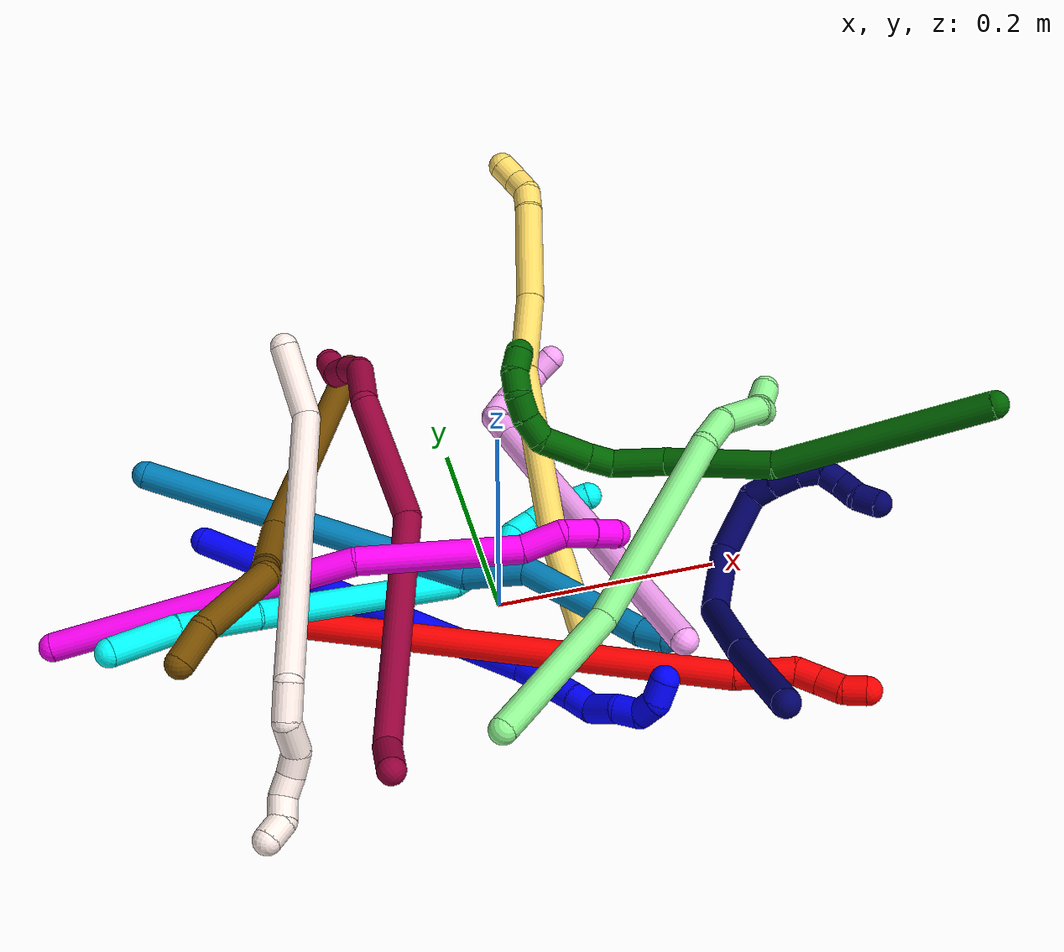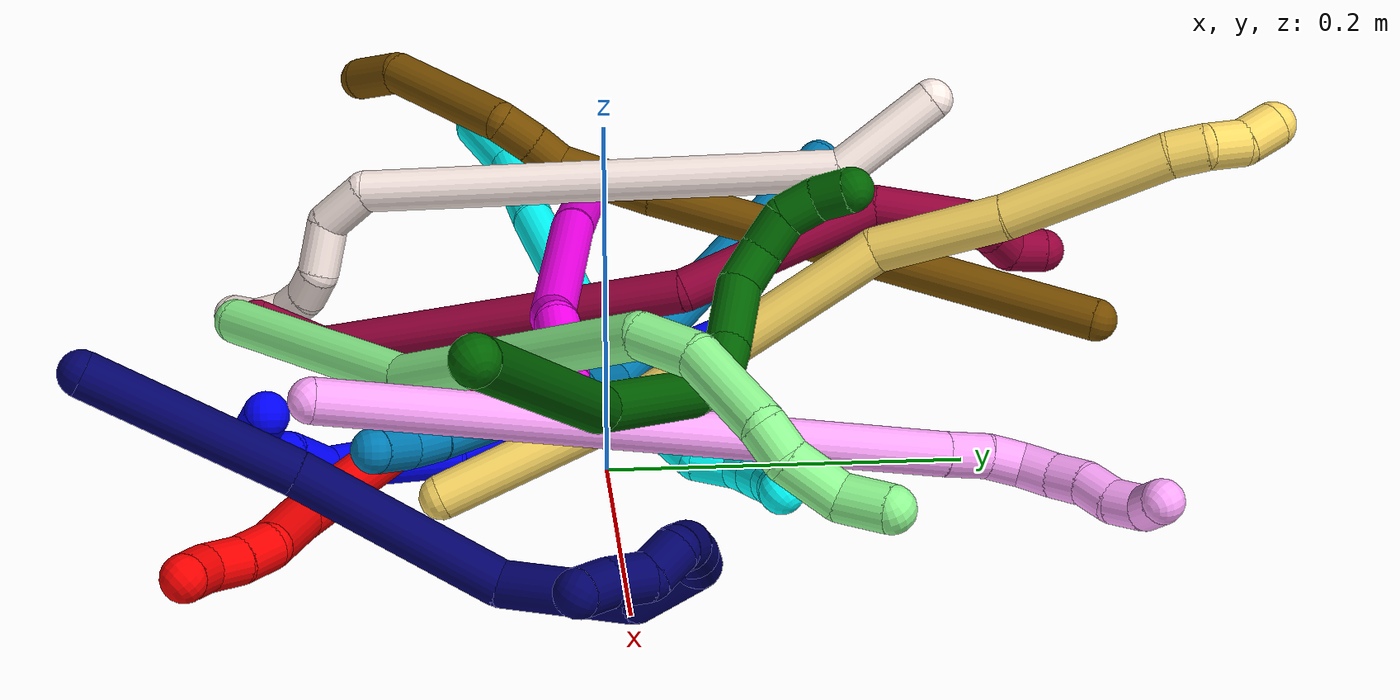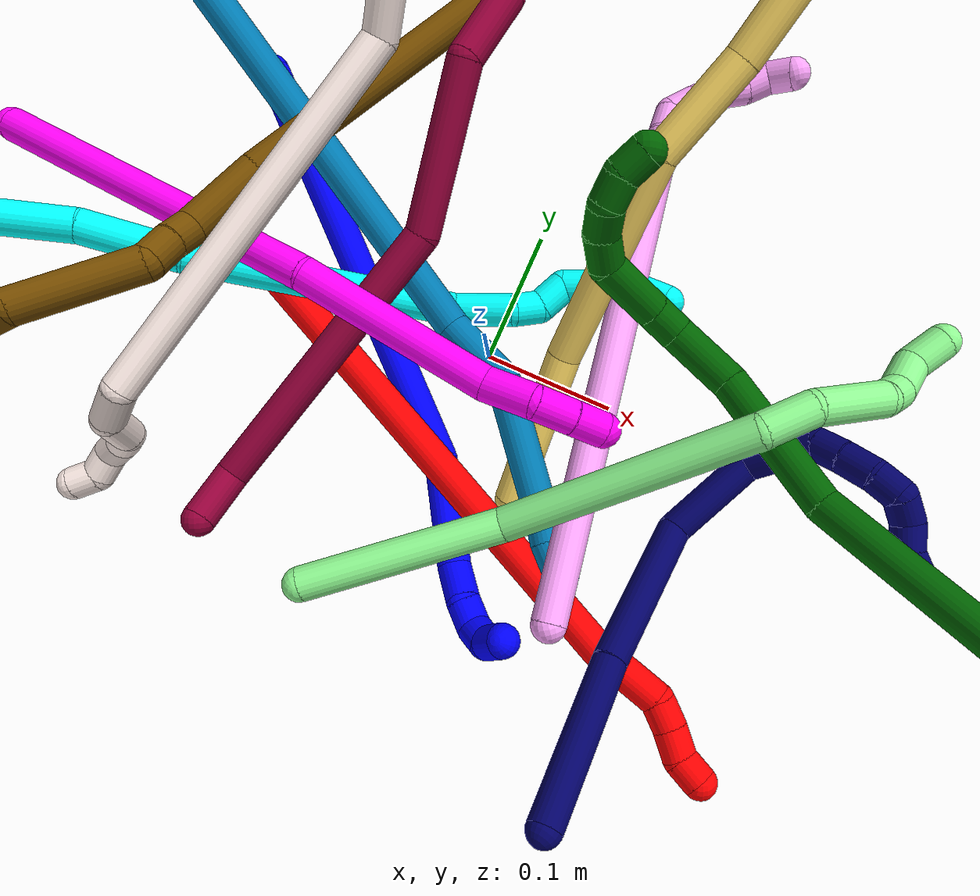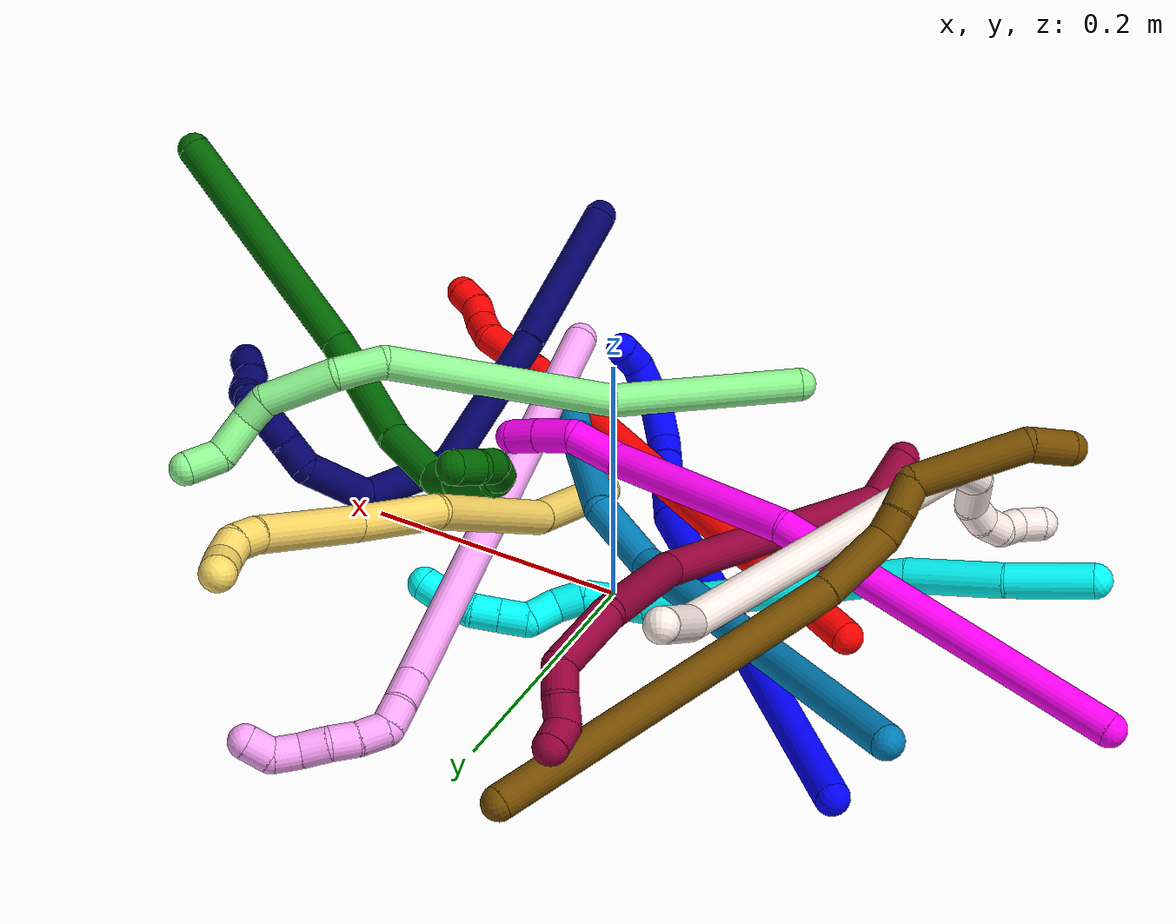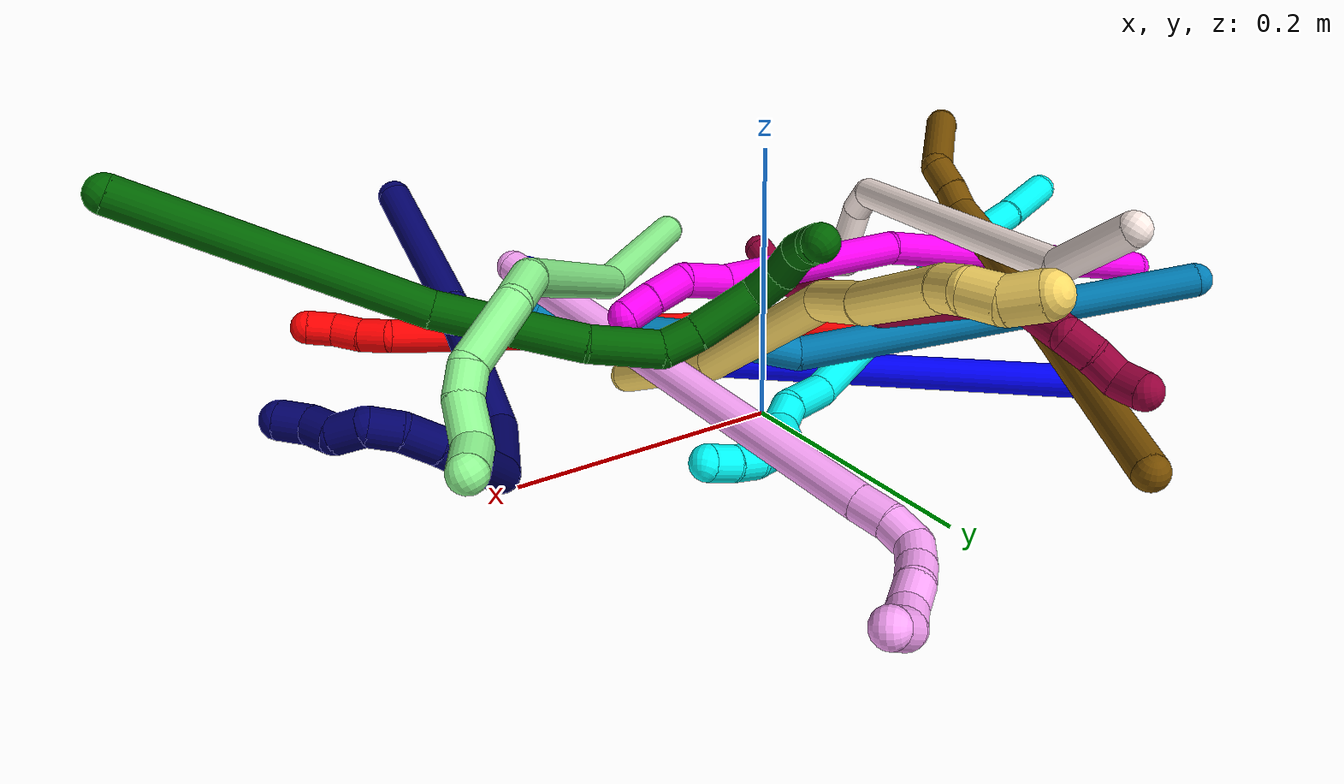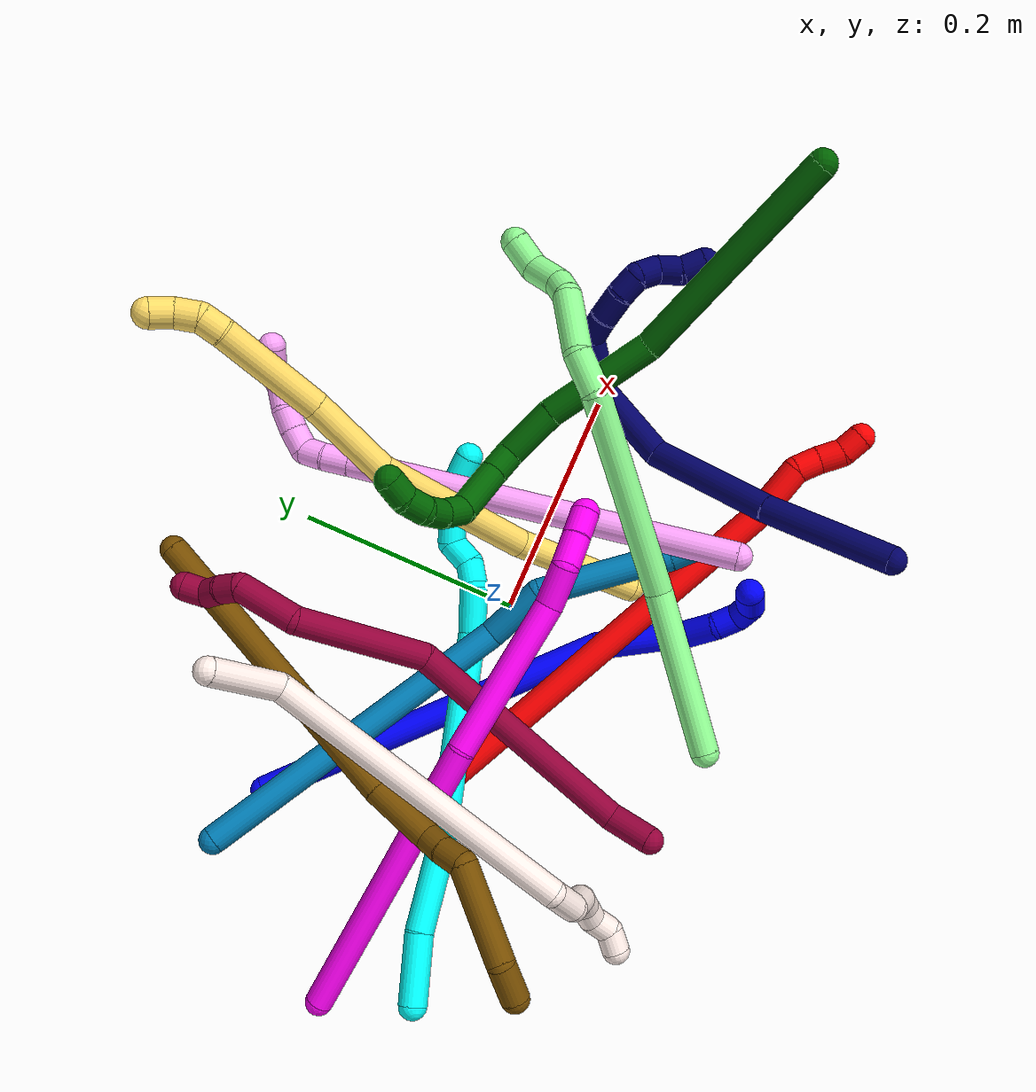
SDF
<sdf version="1.7">
 <world name="default">
  <plugin name="TubeGeneratorPlugin" filename="libtube_generator_plugin.so"/>
  <model name="photoneo_s_sensor">
   <static>1</static>
   <pose>0 0 2 1.57079 1.57079 3.14159</pose>
   <link name="link">
    <inertial><mass>0.1</mass></inertial>
    <sensor name="sensor" type="depth">
     <update_rate>30</update_rate>
     <camera>
      <horizontal_fov>1.22</horizontal_fov>
      <image><width>1920</width><height>1200</height><format>B8G8R8</format></image>
      <clip><near>0.1</near><far>4</far></clip>
      <depth_camera><output>points</output></depth_camera>
     </camera>
     <plugin name="camera_plugin" filename="libgazebo_ros_depth_camera.so">
      <baseline>0.2</baseline>
      <alwaysOn>1</alwaysOn>
      <updateRate>0.0</updateRate>
      <cameraName>camera_ir</cameraName>
      <imageTopicName>/camera/color/image_raw</imageTopicName>
      <cameraInfoTopicName>/camera/color/camera_info</cameraInfoTopicName>
      <depthImageTopicName>/camera/depth/image_raw</depthImageTopicName>
      <depthImageCameraInfoTopicName>/camera/depth/camera_info</depthImageCameraInfoTopicName>
      <pointCloudTopicName>/camera/depth/points</pointCloudTopicName>
      <frameName>fr_optical</frameName>
      <pointCloudCutoff>0.1</pointCloudCutoff>
      <pointCloudCutoffMax>2.0</pointCloudCutoffMax>
      <distortionK1>0</distortionK1>
      <distortionK2>0</distortionK2>
      <distortionK3>0</distortionK3>
      <distortionT1>0</distortionT1>
      <distortionT2>0</distortionT2>
      <CxPrime>0</CxPrime>
      <Cx>0</Cx>
      <Cy>0</Cy>
      <focalLength>0</focalLength>
      <hackBaseline>0</hackBaseline>
     </plugin>
    </sensor>
   </link>
  </model>
  <gravity>0 0 -9.8</gravity>
  <magnetic_field>6e-06 2.3e-05 -4.2e-05</magnetic_field>
  <atmosphere type="adiabatic"/>
  <physics name="default_physics" default="0" type="ode">
   <max_step_size>0.003</max_step_size>
   <real_time_factor>1</real_time_factor>
   <real_time_update_rate>1000</real_time_update_rate>
   <max_contacts>10000</max_contacts>
   <ode>
    <solver>
     <type>quick</type>
     <iters>100</iters>
     <sor>1.3</sor>
     <use_dynamic_moi_rescaling>0</use_dynamic_moi_rescaling>
    </solver>
    <constraints>
     <contact_max_correcting_vel>0</contact_max_correcting_vel>
     <contact_surface_layer>0.001</contact_surface_layer>
     <cfm>0</cfm>
     <erp>0.2</erp>
    </constraints>
   </ode>
  </physics>
  <scene><ambient>0.4 0.4 0.4 1</ambient><background>0.7 0.7 0.7 1</background><shadows>0</shadows></scene>
  <audio><device>default</device></audio>
  <spherical_coordinates>
   <surface_model>EARTH_WGS84</surface_model>
   <latitude_deg>0</latitude_deg>
   <longitude_deg>0</longitude_deg>
   <elevation>0</elevation>
   <heading_deg>0</heading_deg>
  </spherical_coordinates>
  <model name="bin">
   <static>1</static>
   <link name="bottom">
    <collision name="collision-bottom">
     <pose>0 0 -0.01 0 -0 0</pose>
     <geometry><box><size>0.8 0.6 0.02</size></box></geometry>
     <surface>
      <friction><ode><mu>100</mu><mu2>100</mu2></ode></friction>
      <contact><collide_bitmask>65535</collide_bitmask></contact>
     </surface>
    </collision>
   </link>
   <link name="west_wall">
    <collision name="collision-west_wall">
     <pose>-0.41 0 0.1 0 -0 0</pose>
     <geometry><box><size>0.02 0.6 0.2</size></box></geometry>
     <surface>
      <friction><ode><mu>100</mu><mu2>100</mu2></ode></friction>
      <contact><collide_bitmask>65535</collide_bitmask></contact>
     </surface>
    </collision>
   </link>
   <link name="east_wall">
    <collision name="collision-east_wall">
     <pose>0.41 0 0.1 0 -0 0</pose>
     <geometry><box><size>0.02 0.6 0.2</size></box></geometry>
     <surface>
      <friction><ode><mu>100</mu><mu2>100</mu2></ode></friction>
      <contact><collide_bitmask>65535</collide_bitmask></contact>
     </surface>
    </collision>
   </link>
   <link name="south_wall">
    <collision name="collision-south_wall">
     <pose>0 -0.31 0.1 0 -0 0</pose>
     <geometry><box><size>0.8 0.02 0.2</size></box></geometry>
     <surface>
      <friction><ode><mu>100</mu><mu2>100</mu2></ode></friction>
      <contact><collide_bitmask>65535</collide_bitmask></contact>
     </surface>
    </collision>
   </link>
   <link name="north_wall">
    <collision name="collision-north_wall">
     <pose>0 0.31 0.1 0 -0 0</pose>
     <geometry><box><size>0.8 0.02 0.2</size></box></geometry>
     <surface>
      <friction><ode><mu>100</mu><mu2>100</mu2></ode></friction>
      <contact><collide_bitmask>65535</collide_bitmask></contact>
     </surface>
    </collision>
   </link>
  </model>
  <model name="1">
   <static>0</static>
   <link name="1">
    <collision name="collision-cylinder-e_1_1_4">
     <pose>0.120253 -0.10048 0.048038 1.12484 0.823722 0.53739</pose>
     <geometry><cylinder><radius>0.0125</radius><length>0.327809</length></cylinder></geometry>
     <surface>
      <friction><ode><mu>1.16</mu><mu2>1.16</mu2><slip1>0</slip1><slip2>0</slip2></ode></friction>
      <contact><ode><kp>1e+06</kp><kd>1</kd><max_vel>0</max_vel><min_depth>0.001</min_depth></ode></contact>
     </surface>
    </collision>
    <visual name="visual-cylinder-e_1_1_4">
     <pose>0.120253 -0.10048 0.048038 1.12484 0.823722 0.53739</pose>
     <geometry><cylinder><radius>0.0125</radius><length>0.327809</length></cylinder></geometry>
     <material><ambient>0 0 1 1</ambient></material>
    </visual>
    <collision name="collision-cylinder-e_2_4_5">
     <pose>0.267136 -0.215096 0.098072 1.43043 1.07867 0.958882</pose>
     <geometry><cylinder><radius>0.0125</radius><length>0.06043</length></cylinder></geometry>
     <surface>
      <friction><ode><mu>1.16</mu><mu2>1.16</mu2><slip1>0</slip1><slip2>0</slip2></ode></friction>
      <contact><ode><kp>1e+06</kp><kd>1</kd><max_vel>0</max_vel><min_depth>0.001</min_depth></ode></contact>
     </surface>
    </collision>
    <visual name="visual-cylinder-e_2_4_5">
     <pose>0.267136 -0.215096 0.098072 1.43043 1.07867 0.958882</pose>
     <geometry><cylinder><radius>0.0125</radius><length>0.06043</length></cylinder></geometry>
     <material><ambient>0 0 1 1</ambient></material>
    </visual>
    <collision name="collision-cylinder-e_3_5_6">
     <pose>0.302849 -0.23362 0.101478 1.26021 1.1013 0.842002</pose>
     <geometry><cylinder><radius>0.0125</radius><length>0.020371</length></cylinder></geometry>
     <surface>
      <friction><ode><mu>1.16</mu><mu2>1.16</mu2><slip1>0</slip1><slip2>0</slip2></ode></friction>
      <contact><ode><kp>1e+06</kp><kd>1</kd><max_vel>0</max_vel><min_depth>0.001</min_depth></ode></contact>
     </surface>
    </collision>
    <visual name="visual-cylinder-e_3_5_6">
     <pose>0.302849 -0.23362 0.101478 1.26021 1.1013 0.842002</pose>
     <geometry><cylinder><radius>0.0125</radius><length>0.020371</length></cylinder></geometry>
     <material><ambient>0 0 1 1</ambient></material>
    </visual>
    <collision name="collision-cylinder-e_4_6_7">
     <pose>0.322295 -0.248198 0.098809 1.95145 0.756719 1.06196</pose>
     <geometry><cylinder><radius>0.0125</radius><length>0.030191</length></cylinder></geometry>
     <surface>
      <friction><ode><mu>1.16</mu><mu2>1.16</mu2><slip1>0</slip1><slip2>0</slip2></ode></friction>
      <contact><ode><kp>1e+06</kp><kd>1</kd><max_vel>0</max_vel><min_depth>0.001</min_depth></ode></contact>
     </surface>
    </collision>
    <visual name="visual-cylinder-e_4_6_7">
     <pose>0.322295 -0.248198 0.098809 1.95145 0.756719 1.06196</pose>
     <geometry><cylinder><radius>0.0125</radius><length>0.030191</length></cylinder></geometry>
     <material><ambient>0 0 1 1</ambient></material>
    </visual>
    <collision name="collision-cylinder-e_5_7_8">
     <pose>0.340111 -0.265531 0.095661 1.44131 0.802405 0.713251</pose>
     <geometry><cylinder><radius>0.0125</radius><length>0.020728</length></cylinder></geometry>
     <surface>
      <friction><ode><mu>1.16</mu><mu2>1.16</mu2><slip1>0</slip1><slip2>0</slip2></ode></friction>
      <contact><ode><kp>1e+06</kp><kd>1</kd><max_vel>0</max_vel><min_depth>0.001</min_depth></ode></contact>
     </surface>
    </collision>
    <visual name="visual-cylinder-e_5_7_8">
     <pose>0.340111 -0.265531 0.095661 1.44131 0.802405 0.713251</pose>
     <geometry><cylinder><radius>0.0125</radius><length>0.020728</length></cylinder></geometry>
     <material><ambient>0 0 1 1</ambient></material>
    </visual>
    <collision name="collision-cylinder-e_6_8_9">
     <pose>0.350241 -0.281111 0.091806 2.08663 0.269298 0.456973</pose>
     <geometry><cylinder><radius>0.0125</radius><length>0.020126</length></cylinder></geometry>
     <surface>
      <friction><ode><mu>1.16</mu><mu2>1.16</mu2><slip1>0</slip1><slip2>0</slip2></ode></friction>
      <contact><ode><kp>1e+06</kp><kd>1</kd><max_vel>0</max_vel><min_depth>0.001</min_depth></ode></contact>
     </surface>
    </collision>
    <visual name="visual-cylinder-e_6_8_9">
     <pose>0.350241 -0.281111 0.091806 2.08663 0.269298 0.456973</pose>
     <geometry><cylinder><radius>0.0125</radius><length>0.020126</length></cylinder></geometry>
     <material><ambient>0 0 1 1</ambient></material>
    </visual>
    <collision name="collision-cylinder-e_7_9_2">
     <pose>0.349602 -0.297366 0.081419 2.19273 -0.332081 -0.630855</pose>
     <geometry><cylinder><radius>0.0125</radius><length>0.020345</length></cylinder></geometry>
     <surface>
      <friction><ode><mu>1.16</mu><mu2>1.16</mu2><slip1>0</slip1><slip2>0</slip2></ode></friction>
      <contact><ode><kp>1e+06</kp><kd>1</kd><max_vel>0</max_vel><min_depth>0.001</min_depth></ode></contact>
     </surface>
    </collision>
    <visual name="visual-cylinder-e_7_9_2">
     <pose>0.349602 -0.297366 0.081419 2.19273 -0.332081 -0.630855</pose>
     <geometry><cylinder><radius>0.0125</radius><length>0.020345</length></cylinder></geometry>
     <material><ambient>0 0 1 1</ambient></material>
    </visual>
    <collision name="collision-sphere-2">
     <pose>0.346285 -0.305182 0.075816 0 -0 0</pose>
     <geometry><sphere><radius>0.0125</radius></sphere></geometry>
     <surface>
      <friction><ode><mu>1.16</mu><mu2>1.16</mu2><slip1>0</slip1><slip2>0</slip2></ode></friction>
      <contact><ode><kp>1e+06</kp><kd>1</kd><max_vel>0</max_vel><min_depth>0.001</min_depth></ode></contact>
     </surface>
    </collision>
    <visual name="visual-sphere-2">
     <pose>0.346285 -0.305182 0.075816 0 -0 0</pose>
     <geometry><sphere><radius>0.0125</radius></sphere></geometry>
     <material><ambient>0 0 1 1</ambient></material>
    </visual>
    <collision name="collision-sphere-9">
     <pose>0.352918 -0.28955 0.087021 0 -0 0</pose>
     <geometry><sphere><radius>0.0125</radius></sphere></geometry>
     <surface>
      <friction><ode><mu>1.16</mu><mu2>1.16</mu2><slip1>0</slip1><slip2>0</slip2></ode></friction>
      <contact><ode><kp>1e+06</kp><kd>1</kd><max_vel>0</max_vel><min_depth>0.001</min_depth></ode></contact>
     </surface>
    </collision>
    <visual name="visual-sphere-9">
     <pose>0.352918 -0.28955 0.087021 0 -0 0</pose>
     <geometry><sphere><radius>0.0125</radius></sphere></geometry>
     <material><ambient>0 0 1 1</ambient></material>
    </visual>
    <collision name="collision-sphere-4">
     <pose>0.240507 -0.20096 0.096075 0 -0 0</pose>
     <geometry><sphere><radius>0.0125</radius></sphere></geometry>
     <surface>
      <friction><ode><mu>1.16</mu><mu2>1.16</mu2><slip1>0</slip1><slip2>0</slip2></ode></friction>
      <contact><ode><kp>1e+06</kp><kd>1</kd><max_vel>0</max_vel><min_depth>0.001</min_depth></ode></contact>
     </surface>
    </collision>
    <visual name="visual-sphere-4">
     <pose>0.240507 -0.20096 0.096075 0 -0 0</pose>
     <geometry><sphere><radius>0.0125</radius></sphere></geometry>
     <material><ambient>0 0 1 1</ambient></material>
    </visual>
    <collision name="collision-sphere-1">
     <geometry><sphere><radius>0.0125</radius></sphere></geometry>
     <surface>
      <friction><ode><mu>1.16</mu><mu2>1.16</mu2><slip1>0</slip1><slip2>0</slip2></ode></friction>
      <contact><ode><kp>1e+06</kp><kd>1</kd><max_vel>0</max_vel><min_depth>0.001</min_depth></ode></contact>
     </surface>
    </collision>
    <visual name="visual-sphere-1">
     <geometry><sphere><radius>0.0125</radius></sphere></geometry>
     <material><ambient>0 0 1 1</ambient></material>
    </visual>
    <collision name="collision-sphere-8">
     <pose>0.347563 -0.272673 0.096591 0 -0 0</pose>
     <geometry><sphere><radius>0.0125</radius></sphere></geometry>
     <surface>
      <friction><ode><mu>1.16</mu><mu2>1.16</mu2><slip1>0</slip1><slip2>0</slip2></ode></friction>
      <contact><ode><kp>1e+06</kp><kd>1</kd><max_vel>0</max_vel><min_depth>0.001</min_depth></ode></contact>
     </surface>
    </collision>
    <visual name="visual-sphere-8">
     <pose>0.347563 -0.272673 0.096591 0 -0 0</pose>
     <geometry><sphere><radius>0.0125</radius></sphere></geometry>
     <material><ambient>0 0 1 1</ambient></material>
    </visual>
    <collision name="collision-sphere-5">
     <pose>0.293765 -0.229232 0.10007 0 -0 0</pose>
     <geometry><sphere><radius>0.0125</radius></sphere></geometry>
     <surface>
      <friction><ode><mu>1.16</mu><mu2>1.16</mu2><slip1>0</slip1><slip2>0</slip2></ode></friction>
      <contact><ode><kp>1e+06</kp><kd>1</kd><max_vel>0</max_vel><min_depth>0.001</min_depth></ode></contact>
     </surface>
    </collision>
    <visual name="visual-sphere-5">
     <pose>0.293765 -0.229232 0.10007 0 -0 0</pose>
     <geometry><sphere><radius>0.0125</radius></sphere></geometry>
     <material><ambient>0 0 1 1</ambient></material>
    </visual>
    <collision name="collision-sphere-6">
     <pose>0.311932 -0.238008 0.102887 0 -0 0</pose>
     <geometry><sphere><radius>0.0125</radius></sphere></geometry>
     <surface>
      <friction><ode><mu>1.16</mu><mu2>1.16</mu2><slip1>0</slip1><slip2>0</slip2></ode></friction>
      <contact><ode><kp>1e+06</kp><kd>1</kd><max_vel>0</max_vel><min_depth>0.001</min_depth></ode></contact>
     </surface>
    </collision>
    <visual name="visual-sphere-6">
     <pose>0.311932 -0.238008 0.102887 0 -0 0</pose>
     <geometry><sphere><radius>0.0125</radius></sphere></geometry>
     <material><ambient>0 0 1 1</ambient></material>
    </visual>
    <collision name="collision-sphere-7">
     <pose>0.332659 -0.258388 0.094731 0 -0 0</pose>
     <geometry><sphere><radius>0.0125</radius></sphere></geometry>
     <surface>
      <friction><ode><mu>1.16</mu><mu2>1.16</mu2><slip1>0</slip1><slip2>0</slip2></ode></friction>
      <contact><ode><kp>1e+06</kp><kd>1</kd><max_vel>0</max_vel><min_depth>0.001</min_depth></ode></contact>
     </surface>
    </collision>
    <visual name="visual-sphere-7">
     <pose>0.332659 -0.258388 0.094731 0 -0 0</pose>
     <geometry><sphere><radius>0.0125</radius></sphere></geometry>
     <material><ambient>0 0 1 1</ambient></material>
    </visual>
    <inertial>
     <pose>0.185349 -0.150801 0.064422 0 -0 0</pose>
     <mass>0.5</mass>
     <inertia>
      <ixx>0.002795</ixx>
      <ixy>0</ixy>
      <ixz>0</ixz>
      <iyy>0.003123</iyy>
      <iyz>0</iyz>
      <izz>-0.000357</izz>
     </inertia>
    </inertial>
   </link>
   <pose>-0.241599 0.135496 0.011491 -2.71882 -0.021404 -1.49361</pose>
  </model>
  <model name="2">
   <static>0</static>
   <link name="2">
    <collision name="collision-cylinder-e_1_1_4">
     <pose>0.089786 -0.119314 0.121055 0.778157 0.485986 0.202565</pose>
     <geometry><cylinder><radius>0.0125</radius><length>0.384456</length></cylinder></geometry>
     <surface>
      <friction><ode><mu>1.16</mu><mu2>1.16</mu2><slip1>0</slip1><slip2>0</slip2></ode></friction>
      <contact><ode><kp>1e+06</kp><kd>1</kd><max_vel>0</max_vel><min_depth>0.001</min_depth></ode></contact>
     </surface>
    </collision>
    <visual name="visual-cylinder-e_1_1_4">
     <pose>0.089786 -0.119314 0.121055 0.778157 0.485986 0.202565</pose>
     <geometry><cylinder><radius>0.0125</radius><length>0.384456</length></cylinder></geometry>
     <material><ambient>1 0 0 1</ambient></material>
    </visual>
    <collision name="collision-cylinder-e_2_4_5">
     <pose>0.19191 -0.257781 0.254403 1.00017 0.496768 0.275409</pose>
     <geometry><cylinder><radius>0.0125</radius><length>0.051776</length></cylinder></geometry>
     <surface>
      <friction><ode><mu>1.16</mu><mu2>1.16</mu2><slip1>0</slip1><slip2>0</slip2></ode></friction>
      <contact><ode><kp>1e+06</kp><kd>1</kd><max_vel>0</max_vel><min_depth>0.001</min_depth></ode></contact>
     </surface>
    </collision>
    <visual name="visual-cylinder-e_2_4_5">
     <pose>0.19191 -0.257781 0.254403 1.00017 0.496768 0.275409</pose>
     <geometry><cylinder><radius>0.0125</radius><length>0.051776</length></cylinder></geometry>
     <material><ambient>1 0 0 1</ambient></material>
    </visual>
    <collision name="collision-cylinder-e_3_5_6">
     <pose>0.209532 -0.280881 0.275158 0.436424 0.515035 0.116666</pose>
     <geometry><cylinder><radius>0.0125</radius><length>0.021458</length></cylinder></geometry>
     <surface>
      <friction><ode><mu>1.16</mu><mu2>1.16</mu2><slip1>0</slip1><slip2>0</slip2></ode></friction>
      <contact><ode><kp>1e+06</kp><kd>1</kd><max_vel>0</max_vel><min_depth>0.001</min_depth></ode></contact>
     </surface>
    </collision>
    <visual name="visual-cylinder-e_3_5_6">
     <pose>0.209532 -0.280881 0.275158 0.436424 0.515035 0.116666</pose>
     <geometry><cylinder><radius>0.0125</radius><length>0.021458</length></cylinder></geometry>
     <material><ambient>1 0 0 1</ambient></material>
    </visual>
    <collision name="collision-cylinder-e_4_6_7">
     <pose>0.221724 -0.287685 0.29182 0.335328 0.671884 0.118061</pose>
     <geometry><cylinder><radius>0.0125</radius><length>0.022191</length></cylinder></geometry>
     <surface>
      <friction><ode><mu>1.16</mu><mu2>1.16</mu2><slip1>0</slip1><slip2>0</slip2></ode></friction>
      <contact><ode><kp>1e+06</kp><kd>1</kd><max_vel>0</max_vel><min_depth>0.001</min_depth></ode></contact>
     </surface>
    </collision>
    <visual name="visual-cylinder-e_4_6_7">
     <pose>0.221724 -0.287685 0.29182 0.335328 0.671884 0.118061</pose>
     <geometry><cylinder><radius>0.0125</radius><length>0.022191</length></cylinder></geometry>
     <material><ambient>1 0 0 1</ambient></material>
    </visual>
    <collision name="collision-cylinder-e_5_7_2">
     <pose>0.234267 -0.296687 0.305648 0.829284 0.59486 0.268219</pose>
     <geometry><cylinder><radius>0.0125</radius><length>0.020119</length></cylinder></geometry>
     <surface>
      <friction><ode><mu>1.16</mu><mu2>1.16</mu2><slip1>0</slip1><slip2>0</slip2></ode></friction>
      <contact><ode><kp>1e+06</kp><kd>1</kd><max_vel>0</max_vel><min_depth>0.001</min_depth></ode></contact>
     </surface>
    </collision>
    <visual name="visual-cylinder-e_5_7_2">
     <pose>0.234267 -0.296687 0.305648 0.829284 0.59486 0.268219</pose>
     <geometry><cylinder><radius>0.0125</radius><length>0.020119</length></cylinder></geometry>
     <material><ambient>1 0 0 1</ambient></material>
    </visual>
    <collision name="collision-sphere-2">
     <pose>0.239905 -0.302831 0.311275 0 -0 0</pose>
     <geometry><sphere><radius>0.0125</radius></sphere></geometry>
     <surface>
      <friction><ode><mu>1.16</mu><mu2>1.16</mu2><slip1>0</slip1><slip2>0</slip2></ode></friction>
      <contact><ode><kp>1e+06</kp><kd>1</kd><max_vel>0</max_vel><min_depth>0.001</min_depth></ode></contact>
     </surface>
    </collision>
    <visual name="visual-sphere-2">
     <pose>0.239905 -0.302831 0.311275 0 -0 0</pose>
     <geometry><sphere><radius>0.0125</radius></sphere></geometry>
     <material><ambient>1 0 0 1</ambient></material>
    </visual>
    <collision name="collision-sphere-7">
     <pose>0.22863 -0.290543 0.30002 0 -0 0</pose>
     <geometry><sphere><radius>0.0125</radius></sphere></geometry>
     <surface>
      <friction><ode><mu>1.16</mu><mu2>1.16</mu2><slip1>0</slip1><slip2>0</slip2></ode></friction>
      <contact><ode><kp>1e+06</kp><kd>1</kd><max_vel>0</max_vel><min_depth>0.001</min_depth></ode></contact>
     </surface>
    </collision>
    <visual name="visual-sphere-7">
     <pose>0.22863 -0.290543 0.30002 0 -0 0</pose>
     <geometry><sphere><radius>0.0125</radius></sphere></geometry>
     <material><ambient>1 0 0 1</ambient></material>
    </visual>
    <collision name="collision-sphere-6">
     <pose>0.214817 -0.284828 0.28362 0 -0 0</pose>
     <geometry><sphere><radius>0.0125</radius></sphere></geometry>
     <surface>
      <friction><ode><mu>1.16</mu><mu2>1.16</mu2><slip1>0</slip1><slip2>0</slip2></ode></friction>
      <contact><ode><kp>1e+06</kp><kd>1</kd><max_vel>0</max_vel><min_depth>0.001</min_depth></ode></contact>
     </surface>
    </collision>
    <visual name="visual-sphere-6">
     <pose>0.214817 -0.284828 0.28362 0 -0 0</pose>
     <geometry><sphere><radius>0.0125</radius></sphere></geometry>
     <material><ambient>1 0 0 1</ambient></material>
    </visual>
    <collision name="collision-sphere-5">
     <pose>0.204248 -0.276934 0.266696 0 -0 0</pose>
     <geometry><sphere><radius>0.0125</radius></sphere></geometry>
     <surface>
      <friction><ode><mu>1.16</mu><mu2>1.16</mu2><slip1>0</slip1><slip2>0</slip2></ode></friction>
      <contact><ode><kp>1e+06</kp><kd>1</kd><max_vel>0</max_vel><min_depth>0.001</min_depth></ode></contact>
     </surface>
    </collision>
    <visual name="visual-sphere-5">
     <pose>0.204248 -0.276934 0.266696 0 -0 0</pose>
     <geometry><sphere><radius>0.0125</radius></sphere></geometry>
     <material><ambient>1 0 0 1</ambient></material>
    </visual>
    <collision name="collision-sphere-1">
     <geometry><sphere><radius>0.0125</radius></sphere></geometry>
     <surface>
      <friction><ode><mu>1.16</mu><mu2>1.16</mu2><slip1>0</slip1><slip2>0</slip2></ode></friction>
      <contact><ode><kp>1e+06</kp><kd>1</kd><max_vel>0</max_vel><min_depth>0.001</min_depth></ode></contact>
     </surface>
    </collision>
    <visual name="visual-sphere-1">
     <geometry><sphere><radius>0.0125</radius></sphere></geometry>
     <material><ambient>1 0 0 1</ambient></material>
    </visual>
    <collision name="collision-sphere-4">
     <pose>0.179572 -0.238628 0.24211 0 -0 0</pose>
     <geometry><sphere><radius>0.0125</radius></sphere></geometry>
     <surface>
      <friction><ode><mu>1.16</mu><mu2>1.16</mu2><slip1>0</slip1><slip2>0</slip2></ode></friction>
      <contact><ode><kp>1e+06</kp><kd>1</kd><max_vel>0</max_vel><min_depth>0.001</min_depth></ode></contact>
     </surface>
    </collision>
    <visual name="visual-sphere-4">
     <pose>0.179572 -0.238628 0.24211 0 -0 0</pose>
     <geometry><sphere><radius>0.0125</radius></sphere></geometry>
     <material><ambient>1 0 0 1</ambient></material>
    </visual>
    <inertial>
     <pose>0.117169 -0.155196 0.156483 0 -0 0</pose>
     <mass>0.5</mass>
     <inertia>
      <ixx>0.004998</ixx>
      <ixy>0</ixy>
      <ixz>0</ixz>
      <iyy>0.004466</iyy>
      <iyz>0</iyz>
      <izz>0.000757</izz>
     </inertia>
    </inertial>
   </link>
   <pose>-0.185408 -0.00216 0.02988 3.11191 -0.988294 -1.09192</pose>
  </model>
  <model name="3">
   <static>0</static>
   <link name="3">
    <collision name="collision-cylinder-e_1_1_4">
     <pose>0.016263 0.000525 0.026002 -0.020193 0.558822 -0.005794</pose>
     <geometry><cylinder><radius>0.0125</radius><length>0.061348</length></cylinder></geometry>
     <surface>
      <friction><ode><mu>1.16</mu><mu2>1.16</mu2><slip1>0</slip1><slip2>0</slip2></ode></friction>
      <contact><ode><kp>1e+06</kp><kd>1</kd><max_vel>0</max_vel><min_depth>0.001</min_depth></ode></contact>
     </surface>
    </collision>
    <visual name="visual-cylinder-e_1_1_4">
     <pose>0.016263 0.000525 0.026002 -0.020193 0.558822 -0.005794</pose>
     <geometry><cylinder><radius>0.0125</radius><length>0.061348</length></cylinder></geometry>
     <material><ambient>0.003922 1 0.996078 1</ambient></material>
    </visual>
    <collision name="collision-cylinder-e_2_4_5">
     <pose>0.051575 0.007855 0.080685 -0.232957 0.573728 -0.069007</pose>
     <geometry><cylinder><radius>0.0125</radius><length>0.070193</length></cylinder></geometry>
     <surface>
      <friction><ode><mu>1.16</mu><mu2>1.16</mu2><slip1>0</slip1><slip2>0</slip2></ode></friction>
      <contact><ode><kp>1e+06</kp><kd>1</kd><max_vel>0</max_vel><min_depth>0.001</min_depth></ode></contact>
     </surface>
    </collision>
    <visual name="visual-cylinder-e_2_4_5">
     <pose>0.051575 0.007855 0.080685 -0.232957 0.573728 -0.069007</pose>
     <geometry><cylinder><radius>0.0125</radius><length>0.070193</length></cylinder></geometry>
     <material><ambient>0.003922 1 0.996078 1</ambient></material>
    </visual>
    <collision name="collision-cylinder-e_3_5_6">
     <pose>0.110547 0.030333 0.198099 -0.174826 0.417075 -0.037086</pose>
     <geometry><cylinder><radius>0.0125</radius><length>0.19711</length></cylinder></geometry>
     <surface>
      <friction><ode><mu>1.16</mu><mu2>1.16</mu2><slip1>0</slip1><slip2>0</slip2></ode></friction>
      <contact><ode><kp>1e+06</kp><kd>1</kd><max_vel>0</max_vel><min_depth>0.001</min_depth></ode></contact>
     </surface>
    </collision>
    <visual name="visual-cylinder-e_3_5_6">
     <pose>0.110547 0.030333 0.198099 -0.174826 0.417075 -0.037086</pose>
     <geometry><cylinder><radius>0.0125</radius><length>0.19711</length></cylinder></geometry>
     <material><ambient>0.003922 1 0.996078 1</ambient></material>
    </visual>
    <collision name="collision-cylinder-e_4_6_7">
     <pose>0.16507 0.042763 0.303069 0.197136 0.722635 0.074707</pose>
     <geometry><cylinder><radius>0.0125</radius><length>0.044149</length></cylinder></geometry>
     <surface>
      <friction><ode><mu>1.16</mu><mu2>1.16</mu2><slip1>0</slip1><slip2>0</slip2></ode></friction>
      <contact><ode><kp>1e+06</kp><kd>1</kd><max_vel>0</max_vel><min_depth>0.001</min_depth></ode></contact>
     </surface>
    </collision>
    <visual name="visual-cylinder-e_4_6_7">
     <pose>0.16507 0.042763 0.303069 0.197136 0.722635 0.074707</pose>
     <geometry><cylinder><radius>0.0125</radius><length>0.044149</length></cylinder></geometry>
     <material><ambient>0.003922 1 0.996078 1</ambient></material>
    </visual>
    <collision name="collision-cylinder-e_5_7_8">
     <pose>0.182467 0.038363 0.329757 0.110209 0.260022 0.014424</pose>
     <geometry><cylinder><radius>0.0125</radius><length>0.021762</length></cylinder></geometry>
     <surface>
      <friction><ode><mu>1.16</mu><mu2>1.16</mu2><slip1>0</slip1><slip2>0</slip2></ode></friction>
      <contact><ode><kp>1e+06</kp><kd>1</kd><max_vel>0</max_vel><min_depth>0.001</min_depth></ode></contact>
     </surface>
    </collision>
    <visual name="visual-cylinder-e_5_7_8">
     <pose>0.182467 0.038363 0.329757 0.110209 0.260022 0.014424</pose>
     <geometry><cylinder><radius>0.0125</radius><length>0.021762</length></cylinder></geometry>
     <material><ambient>0.003922 1 0.996078 1</ambient></material>
    </visual>
    <collision name="collision-cylinder-e_6_8_9">
     <pose>0.186066 0.029621 0.349742 0.672115 0.065709 0.02296</pose>
     <geometry><cylinder><radius>0.0125</radius><length>0.024419</length></cylinder></geometry>
     <surface>
      <friction><ode><mu>1.16</mu><mu2>1.16</mu2><slip1>0</slip1><slip2>0</slip2></ode></friction>
      <contact><ode><kp>1e+06</kp><kd>1</kd><max_vel>0</max_vel><min_depth>0.001</min_depth></ode></contact>
     </surface>
    </collision>
    <visual name="visual-cylinder-e_6_8_9">
     <pose>0.186066 0.029621 0.349742 0.672115 0.065709 0.02296</pose>
     <geometry><cylinder><radius>0.0125</radius><length>0.024419</length></cylinder></geometry>
     <material><ambient>0.003922 1 0.996078 1</ambient></material>
    </visual>
    <collision name="collision-cylinder-e_7_9_10">
     <pose>0.193883 0.020357 0.366862 0.217707 0.734336 0.084015</pose>
     <geometry><cylinder><radius>0.0125</radius><length>0.020937</length></cylinder></geometry>
     <surface>
      <friction><ode><mu>1.16</mu><mu2>1.16</mu2><slip1>0</slip1><slip2>0</slip2></ode></friction>
      <contact><ode><kp>1e+06</kp><kd>1</kd><max_vel>0</max_vel><min_depth>0.001</min_depth></ode></contact>
     </surface>
    </collision>
    <visual name="visual-cylinder-e_7_9_10">
     <pose>0.193883 0.020357 0.366862 0.217707 0.734336 0.084015</pose>
     <geometry><cylinder><radius>0.0125</radius><length>0.020937</length></cylinder></geometry>
     <material><ambient>0.003922 1 0.996078 1</ambient></material>
    </visual>
    <collision name="collision-cylinder-e_8_10_11">
     <pose>0.20769 0.017148 0.38166 0.209192 0.744554 0.08194</pose>
     <geometry><cylinder><radius>0.0125</radius><length>0.020046</length></cylinder></geometry>
     <surface>
      <friction><ode><mu>1.16</mu><mu2>1.16</mu2><slip1>0</slip1><slip2>0</slip2></ode></friction>
      <contact><ode><kp>1e+06</kp><kd>1</kd><max_vel>0</max_vel><min_depth>0.001</min_depth></ode></contact>
     </surface>
    </collision>
    <visual name="visual-cylinder-e_8_10_11">
     <pose>0.20769 0.017148 0.38166 0.209192 0.744554 0.08194</pose>
     <geometry><cylinder><radius>0.0125</radius><length>0.020046</length></cylinder></geometry>
     <material><ambient>0.003922 1 0.996078 1</ambient></material>
    </visual>
    <collision name="collision-cylinder-e_9_11_12">
     <pose>0.222792 0.015783 0.394451 -0.029711 0.979212 -0.015834</pose>
     <geometry><cylinder><radius>0.0125</radius><length>0.020024</length></cylinder></geometry>
     <surface>
      <friction><ode><mu>1.16</mu><mu2>1.16</mu2><slip1>0</slip1><slip2>0</slip2></ode></friction>
      <contact><ode><kp>1e+06</kp><kd>1</kd><max_vel>0</max_vel><min_depth>0.001</min_depth></ode></contact>
     </surface>
    </collision>
    <visual name="visual-cylinder-e_9_11_12">
     <pose>0.222792 0.015783 0.394451 -0.029711 0.979212 -0.015834</pose>
     <geometry><cylinder><radius>0.0125</radius><length>0.020024</length></cylinder></geometry>
     <material><ambient>0.003922 1 0.996078 1</ambient></material>
    </visual>
    <collision name="collision-cylinder-e_10_12_2">
     <pose>0.240052 0.017003 0.404382 -0.237856 1.107 -0.147409</pose>
     <geometry><cylinder><radius>0.0125</radius><length>0.020013</length></cylinder></geometry>
     <surface>
      <friction><ode><mu>1.16</mu><mu2>1.16</mu2><slip1>0</slip1><slip2>0</slip2></ode></friction>
      <contact><ode><kp>1e+06</kp><kd>1</kd><max_vel>0</max_vel><min_depth>0.001</min_depth></ode></contact>
     </surface>
    </collision>
    <visual name="visual-cylinder-e_10_12_2">
     <pose>0.240052 0.017003 0.404382 -0.237856 1.107 -0.147409</pose>
     <geometry><cylinder><radius>0.0125</radius><length>0.020013</length></cylinder></geometry>
     <material><ambient>0.003922 1 0.996078 1</ambient></material>
    </visual>
    <collision name="collision-sphere-2">
     <pose>0.249001 0.018058 0.408732 0 -0 0</pose>
     <geometry><sphere><radius>0.0125</radius></sphere></geometry>
     <surface>
      <friction><ode><mu>1.16</mu><mu2>1.16</mu2><slip1>0</slip1><slip2>0</slip2></ode></friction>
      <contact><ode><kp>1e+06</kp><kd>1</kd><max_vel>0</max_vel><min_depth>0.001</min_depth></ode></contact>
     </surface>
    </collision>
    <visual name="visual-sphere-2">
     <pose>0.249001 0.018058 0.408732 0 -0 0</pose>
     <geometry><sphere><radius>0.0125</radius></sphere></geometry>
     <material><ambient>0.003922 1 0.996078 1</ambient></material>
    </visual>
    <collision name="collision-sphere-12">
     <pose>0.231103 0.015949 0.400032 0 -0 0</pose>
     <geometry><sphere><radius>0.0125</radius></sphere></geometry>
     <surface>
      <friction><ode><mu>1.16</mu><mu2>1.16</mu2><slip1>0</slip1><slip2>0</slip2></ode></friction>
      <contact><ode><kp>1e+06</kp><kd>1</kd><max_vel>0</max_vel><min_depth>0.001</min_depth></ode></contact>
     </surface>
    </collision>
    <visual name="visual-sphere-12">
     <pose>0.231103 0.015949 0.400032 0 -0 0</pose>
     <geometry><sphere><radius>0.0125</radius></sphere></geometry>
     <material><ambient>0.003922 1 0.996078 1</ambient></material>
    </visual>
    <collision name="collision-sphere-11">
     <pose>0.214482 0.015617 0.38887 0 -0 0</pose>
     <geometry><sphere><radius>0.0125</radius></sphere></geometry>
     <surface>
      <friction><ode><mu>1.16</mu><mu2>1.16</mu2><slip1>0</slip1><slip2>0</slip2></ode></friction>
      <contact><ode><kp>1e+06</kp><kd>1</kd><max_vel>0</max_vel><min_depth>0.001</min_depth></ode></contact>
     </surface>
    </collision>
    <visual name="visual-sphere-11">
     <pose>0.214482 0.015617 0.38887 0 -0 0</pose>
     <geometry><sphere><radius>0.0125</radius></sphere></geometry>
     <material><ambient>0.003922 1 0.996078 1</ambient></material>
    </visual>
    <collision name="collision-sphere-10">
     <pose>0.200898 0.018678 0.37445 0 -0 0</pose>
     <geometry><sphere><radius>0.0125</radius></sphere></geometry>
     <surface>
      <friction><ode><mu>1.16</mu><mu2>1.16</mu2><slip1>0</slip1><slip2>0</slip2></ode></friction>
      <contact><ode><kp>1e+06</kp><kd>1</kd><max_vel>0</max_vel><min_depth>0.001</min_depth></ode></contact>
     </surface>
    </collision>
    <visual name="visual-sphere-10">
     <pose>0.200898 0.018678 0.37445 0 -0 0</pose>
     <geometry><sphere><radius>0.0125</radius></sphere></geometry>
     <material><ambient>0.003922 1 0.996078 1</ambient></material>
    </visual>
    <collision name="collision-sphere-9">
     <pose>0.186868 0.022035 0.359275 0 -0 0</pose>
     <geometry><sphere><radius>0.0125</radius></sphere></geometry>
     <surface>
      <friction><ode><mu>1.16</mu><mu2>1.16</mu2><slip1>0</slip1><slip2>0</slip2></ode></friction>
      <contact><ode><kp>1e+06</kp><kd>1</kd><max_vel>0</max_vel><min_depth>0.001</min_depth></ode></contact>
     </surface>
    </collision>
    <visual name="visual-sphere-9">
     <pose>0.186868 0.022035 0.359275 0 -0 0</pose>
     <geometry><sphere><radius>0.0125</radius></sphere></geometry>
     <material><ambient>0.003922 1 0.996078 1</ambient></material>
    </visual>
    <collision name="collision-sphere-4">
     <pose>0.032526 0.00105 0.052005 0 -0 0</pose>
     <geometry><sphere><radius>0.0125</radius></sphere></geometry>
     <surface>
      <friction><ode><mu>1.16</mu><mu2>1.16</mu2><slip1>0</slip1><slip2>0</slip2></ode></friction>
      <contact><ode><kp>1e+06</kp><kd>1</kd><max_vel>0</max_vel><min_depth>0.001</min_depth></ode></contact>
     </surface>
    </collision>
    <visual name="visual-sphere-4">
     <pose>0.032526 0.00105 0.052005 0 -0 0</pose>
     <geometry><sphere><radius>0.0125</radius></sphere></geometry>
     <material><ambient>0.003922 1 0.996078 1</ambient></material>
    </visual>
    <collision name="collision-sphere-1">
     <geometry><sphere><radius>0.0125</radius></sphere></geometry>
     <surface>
      <friction><ode><mu>1.16</mu><mu2>1.16</mu2><slip1>0</slip1><slip2>0</slip2></ode></friction>
      <contact><ode><kp>1e+06</kp><kd>1</kd><max_vel>0</max_vel><min_depth>0.001</min_depth></ode></contact>
     </surface>
    </collision>
    <visual name="visual-sphere-1">
     <geometry><sphere><radius>0.0125</radius></sphere></geometry>
     <material><ambient>0.003922 1 0.996078 1</ambient></material>
    </visual>
    <collision name="collision-sphere-8">
     <pose>0.185264 0.037207 0.340208 0 -0 0</pose>
     <geometry><sphere><radius>0.0125</radius></sphere></geometry>
     <surface>
      <friction><ode><mu>1.16</mu><mu2>1.16</mu2><slip1>0</slip1><slip2>0</slip2></ode></friction>
      <contact><ode><kp>1e+06</kp><kd>1</kd><max_vel>0</max_vel><min_depth>0.001</min_depth></ode></contact>
     </surface>
    </collision>
    <visual name="visual-sphere-8">
     <pose>0.185264 0.037207 0.340208 0 -0 0</pose>
     <geometry><sphere><radius>0.0125</radius></sphere></geometry>
     <material><ambient>0.003922 1 0.996078 1</ambient></material>
    </visual>
    <collision name="collision-sphere-5">
     <pose>0.070624 0.01466 0.109366 0 -0 0</pose>
     <geometry><sphere><radius>0.0125</radius></sphere></geometry>
     <surface>
      <friction><ode><mu>1.16</mu><mu2>1.16</mu2><slip1>0</slip1><slip2>0</slip2></ode></friction>
      <contact><ode><kp>1e+06</kp><kd>1</kd><max_vel>0</max_vel><min_depth>0.001</min_depth></ode></contact>
     </surface>
    </collision>
    <visual name="visual-sphere-5">
     <pose>0.070624 0.01466 0.109366 0 -0 0</pose>
     <geometry><sphere><radius>0.0125</radius></sphere></geometry>
     <material><ambient>0.003922 1 0.996078 1</ambient></material>
    </visual>
    <collision name="collision-sphere-6">
     <pose>0.150471 0.046006 0.286832 0 -0 0</pose>
     <geometry><sphere><radius>0.0125</radius></sphere></geometry>
     <surface>
      <friction><ode><mu>1.16</mu><mu2>1.16</mu2><slip1>0</slip1><slip2>0</slip2></ode></friction>
      <contact><ode><kp>1e+06</kp><kd>1</kd><max_vel>0</max_vel><min_depth>0.001</min_depth></ode></contact>
     </surface>
    </collision>
    <visual name="visual-sphere-6">
     <pose>0.150471 0.046006 0.286832 0 -0 0</pose>
     <geometry><sphere><radius>0.0125</radius></sphere></geometry>
     <material><ambient>0.003922 1 0.996078 1</ambient></material>
    </visual>
    <collision name="collision-sphere-7">
     <pose>0.179669 0.03952 0.319305 0 -0 0</pose>
     <geometry><sphere><radius>0.0125</radius></sphere></geometry>
     <surface>
      <friction><ode><mu>1.16</mu><mu2>1.16</mu2><slip1>0</slip1><slip2>0</slip2></ode></friction>
      <contact><ode><kp>1e+06</kp><kd>1</kd><max_vel>0</max_vel><min_depth>0.001</min_depth></ode></contact>
     </surface>
    </collision>
    <visual name="visual-sphere-7">
     <pose>0.179669 0.03952 0.319305 0 -0 0</pose>
     <geometry><sphere><radius>0.0125</radius></sphere></geometry>
     <material><ambient>0.003922 1 0.996078 1</ambient></material>
    </visual>
    <inertial>
     <pose>0.119396 0.02287 0.213452 0 -0 0</pose>
     <mass>0.5</mass>
     <inertia>
      <ixx>0.000645</ixx>
      <ixy>0</ixy>
      <ixz>0</ixz>
      <iyy>0.000686</iyy>
      <iyz>0</iyz>
      <izz>-0.000375</izz>
     </inertia>
    </inertial>
   </link>
   <pose>-0.342694 -0.061114 0.099131 -2.38697 -0.714586 -0.28028</pose>
  </model>
  <model name="4">
   <static>0</static>
   <link name="4">
    <collision name="collision-cylinder-e_1_1_4">
     <pose>-0.055426 0.083346 0.145244 -0.520955 -0.319634 0.085873</pose>
     <geometry><cylinder><radius>0.0125</radius><length>0.352785</length></cylinder></geometry>
     <surface>
      <friction><ode><mu>1.16</mu><mu2>1.16</mu2><slip1>0</slip1><slip2>0</slip2></ode></friction>
      <contact><ode><kp>1e+06</kp><kd>1</kd><max_vel>0</max_vel><min_depth>0.001</min_depth></ode></contact>
     </surface>
    </collision>
    <visual name="visual-cylinder-e_1_1_4">
     <pose>-0.055426 0.083346 0.145244 -0.520955 -0.319634 0.085873</pose>
     <geometry><cylinder><radius>0.0125</radius><length>0.352785</length></cylinder></geometry>
     <material><ambient>1 0.65098 0.996078 1</ambient></material>
    </visual>
    <collision name="collision-cylinder-e_2_4_5">
     <pose>-0.114283 0.172368 0.300697 -0.507495 -0.285699 0.074566</pose>
     <geometry><cylinder><radius>0.0125</radius><length>0.024349</length></cylinder></geometry>
     <surface>
      <friction><ode><mu>1.16</mu><mu2>1.16</mu2><slip1>0</slip1><slip2>0</slip2></ode></friction>
      <contact><ode><kp>1e+06</kp><kd>1</kd><max_vel>0</max_vel><min_depth>0.001</min_depth></ode></contact>
     </surface>
    </collision>
    <visual name="visual-cylinder-e_2_4_5">
     <pose>-0.114283 0.172368 0.300697 -0.507495 -0.285699 0.074566</pose>
     <geometry><cylinder><radius>0.0125</radius><length>0.024349</length></cylinder></geometry>
     <material><ambient>1 0.65098 0.996078 1</ambient></material>
    </visual>
    <collision name="collision-cylinder-e_3_5_6">
     <pose>-0.122227 0.183393 0.318552 -0.610331 -0.45049 0.144106</pose>
     <geometry><cylinder><radius>0.0125</radius><length>0.02073</length></cylinder></geometry>
     <surface>
      <friction><ode><mu>1.16</mu><mu2>1.16</mu2><slip1>0</slip1><slip2>0</slip2></ode></friction>
      <contact><ode><kp>1e+06</kp><kd>1</kd><max_vel>0</max_vel><min_depth>0.001</min_depth></ode></contact>
     </surface>
    </collision>
    <visual name="visual-cylinder-e_3_5_6">
     <pose>-0.122227 0.183393 0.318552 -0.610331 -0.45049 0.144106</pose>
     <geometry><cylinder><radius>0.0125</radius><length>0.02073</length></cylinder></geometry>
     <material><ambient>1 0.65098 0.996078 1</ambient></material>
    </visual>
    <collision name="collision-cylinder-e_4_6_7">
     <pose>-0.128233 0.199002 0.328495 -1.35065 -0.141028 0.113024</pose>
     <geometry><cylinder><radius>0.0125</radius><length>0.021241</length></cylinder></geometry>
     <surface>
      <friction><ode><mu>1.16</mu><mu2>1.16</mu2><slip1>0</slip1><slip2>0</slip2></ode></friction>
      <contact><ode><kp>1e+06</kp><kd>1</kd><max_vel>0</max_vel><min_depth>0.001</min_depth></ode></contact>
     </surface>
    </collision>
    <visual name="visual-cylinder-e_4_6_7">
     <pose>-0.128233 0.199002 0.328495 -1.35065 -0.141028 0.113024</pose>
     <geometry><cylinder><radius>0.0125</radius><length>0.021241</length></cylinder></geometry>
     <material><ambient>1 0.65098 0.996078 1</ambient></material>
    </visual>
    <collision name="collision-cylinder-e_5_7_8">
     <pose>-0.129752 0.21929 0.332004 -1.45047 -0.002544 0.002255</pose>
     <geometry><cylinder><radius>0.0125</radius><length>0.020198</length></cylinder></geometry>
     <surface>
      <friction><ode><mu>1.16</mu><mu2>1.16</mu2><slip1>0</slip1><slip2>0</slip2></ode></friction>
      <contact><ode><kp>1e+06</kp><kd>1</kd><max_vel>0</max_vel><min_depth>0.001</min_depth></ode></contact>
     </surface>
    </collision>
    <visual name="visual-cylinder-e_5_7_8">
     <pose>-0.129752 0.21929 0.332004 -1.45047 -0.002544 0.002255</pose>
     <geometry><cylinder><radius>0.0125</radius><length>0.020198</length></cylinder></geometry>
     <material><ambient>1 0.65098 0.996078 1</ambient></material>
    </visual>
    <collision name="collision-cylinder-e_6_8_9">
     <pose>-0.131957 0.239368 0.332504 -1.64154 -0.212978 0.228474</pose>
     <geometry><cylinder><radius>0.0125</radius><length>0.02062</length></cylinder></geometry>
     <surface>
      <friction><ode><mu>1.16</mu><mu2>1.16</mu2><slip1>0</slip1><slip2>0</slip2></ode></friction>
      <contact><ode><kp>1e+06</kp><kd>1</kd><max_vel>0</max_vel><min_depth>0.001</min_depth></ode></contact>
     </surface>
    </collision>
    <visual name="visual-cylinder-e_6_8_9">
     <pose>-0.131957 0.239368 0.332504 -1.64154 -0.212978 0.228474</pose>
     <geometry><cylinder><radius>0.0125</radius><length>0.02062</length></cylinder></geometry>
     <material><ambient>1 0.65098 0.996078 1</ambient></material>
    </visual>
    <collision name="collision-cylinder-e_7_9_10">
     <pose>-0.133992 0.259345 0.333253 -1.4246 0.014391 -0.012428</pose>
     <geometry><cylinder><radius>0.0125</radius><length>0.020067</length></cylinder></geometry>
     <surface>
      <friction><ode><mu>1.16</mu><mu2>1.16</mu2><slip1>0</slip1><slip2>0</slip2></ode></friction>
      <contact><ode><kp>1e+06</kp><kd>1</kd><max_vel>0</max_vel><min_depth>0.001</min_depth></ode></contact>
     </surface>
    </collision>
    <visual name="visual-cylinder-e_7_9_10">
     <pose>-0.133992 0.259345 0.333253 -1.4246 0.014391 -0.012428</pose>
     <geometry><cylinder><radius>0.0125</radius><length>0.020067</length></cylinder></geometry>
     <material><ambient>1 0.65098 0.996078 1</ambient></material>
    </visual>
    <collision name="collision-cylinder-e_8_10_2">
     <pose>-0.128511 0.277497 0.332729 -1.80757 0.562591 -0.703433</pose>
     <geometry><cylinder><radius>0.0125</radius><length>0.020008</length></cylinder></geometry>
     <surface>
      <friction><ode><mu>1.16</mu><mu2>1.16</mu2><slip1>0</slip1><slip2>0</slip2></ode></friction>
      <contact><ode><kp>1e+06</kp><kd>1</kd><max_vel>0</max_vel><min_depth>0.001</min_depth></ode></contact>
     </surface>
    </collision>
    <visual name="visual-cylinder-e_8_10_2">
     <pose>-0.128511 0.277497 0.332729 -1.80757 0.562591 -0.703433</pose>
     <geometry><cylinder><radius>0.0125</radius><length>0.020008</length></cylinder></geometry>
     <material><ambient>1 0.65098 0.996078 1</ambient></material>
    </visual>
    <collision name="collision-sphere-2">
     <pose>-0.123175 0.285723 0.330744 0 -0 0</pose>
     <geometry><sphere><radius>0.0125</radius></sphere></geometry>
     <surface>
      <friction><ode><mu>1.16</mu><mu2>1.16</mu2><slip1>0</slip1><slip2>0</slip2></ode></friction>
      <contact><ode><kp>1e+06</kp><kd>1</kd><max_vel>0</max_vel><min_depth>0.001</min_depth></ode></contact>
     </surface>
    </collision>
    <visual name="visual-sphere-2">
     <pose>-0.123175 0.285723 0.330744 0 -0 0</pose>
     <geometry><sphere><radius>0.0125</radius></sphere></geometry>
     <material><ambient>1 0.65098 0.996078 1</ambient></material>
    </visual>
    <collision name="collision-sphere-10">
     <pose>-0.133847 0.269271 0.334714 0 -0 0</pose>
     <geometry><sphere><radius>0.0125</radius></sphere></geometry>
     <surface>
      <friction><ode><mu>1.16</mu><mu2>1.16</mu2><slip1>0</slip1><slip2>0</slip2></ode></friction>
      <contact><ode><kp>1e+06</kp><kd>1</kd><max_vel>0</max_vel><min_depth>0.001</min_depth></ode></contact>
     </surface>
    </collision>
    <visual name="visual-sphere-10">
     <pose>-0.133847 0.269271 0.334714 0 -0 0</pose>
     <geometry><sphere><radius>0.0125</radius></sphere></geometry>
     <material><ambient>1 0.65098 0.996078 1</ambient></material>
    </visual>
    <collision name="collision-sphere-9">
     <pose>-0.134136 0.24942 0.331791 0 -0 0</pose>
     <geometry><sphere><radius>0.0125</radius></sphere></geometry>
     <surface>
      <friction><ode><mu>1.16</mu><mu2>1.16</mu2><slip1>0</slip1><slip2>0</slip2></ode></friction>
      <contact><ode><kp>1e+06</kp><kd>1</kd><max_vel>0</max_vel><min_depth>0.001</min_depth></ode></contact>
     </surface>
    </collision>
    <visual name="visual-sphere-9">
     <pose>-0.134136 0.24942 0.331791 0 -0 0</pose>
     <geometry><sphere><radius>0.0125</radius></sphere></geometry>
     <material><ambient>1 0.65098 0.996078 1</ambient></material>
    </visual>
    <collision name="collision-sphere-4">
     <pose>-0.110852 0.166691 0.290488 0 -0 0</pose>
     <geometry><sphere><radius>0.0125</radius></sphere></geometry>
     <surface>
      <friction><ode><mu>1.16</mu><mu2>1.16</mu2><slip1>0</slip1><slip2>0</slip2></ode></friction>
      <contact><ode><kp>1e+06</kp><kd>1</kd><max_vel>0</max_vel><min_depth>0.001</min_depth></ode></contact>
     </surface>
    </collision>
    <visual name="visual-sphere-4">
     <pose>-0.110852 0.166691 0.290488 0 -0 0</pose>
     <geometry><sphere><radius>0.0125</radius></sphere></geometry>
     <material><ambient>1 0.65098 0.996078 1</ambient></material>
    </visual>
    <collision name="collision-sphere-1">
     <geometry><sphere><radius>0.0125</radius></sphere></geometry>
     <surface>
      <friction><ode><mu>1.16</mu><mu2>1.16</mu2><slip1>0</slip1><slip2>0</slip2></ode></friction>
      <contact><ode><kp>1e+06</kp><kd>1</kd><max_vel>0</max_vel><min_depth>0.001</min_depth></ode></contact>
     </surface>
    </collision>
    <visual name="visual-sphere-1">
     <geometry><sphere><radius>0.0125</radius></sphere></geometry>
     <material><ambient>1 0.65098 0.996078 1</ambient></material>
    </visual>
    <collision name="collision-sphere-8">
     <pose>-0.129778 0.229316 0.333216 0 -0 0</pose>
     <geometry><sphere><radius>0.0125</radius></sphere></geometry>
     <surface>
      <friction><ode><mu>1.16</mu><mu2>1.16</mu2><slip1>0</slip1><slip2>0</slip2></ode></friction>
      <contact><ode><kp>1e+06</kp><kd>1</kd><max_vel>0</max_vel><min_depth>0.001</min_depth></ode></contact>
     </surface>
    </collision>
    <visual name="visual-sphere-8">
     <pose>-0.129778 0.229316 0.333216 0 -0 0</pose>
     <geometry><sphere><radius>0.0125</radius></sphere></geometry>
     <material><ambient>1 0.65098 0.996078 1</ambient></material>
    </visual>
    <collision name="collision-sphere-5">
     <pose>-0.117714 0.178045 0.310906 0 -0 0</pose>
     <geometry><sphere><radius>0.0125</radius></sphere></geometry>
     <surface>
      <friction><ode><mu>1.16</mu><mu2>1.16</mu2><slip1>0</slip1><slip2>0</slip2></ode></friction>
      <contact><ode><kp>1e+06</kp><kd>1</kd><max_vel>0</max_vel><min_depth>0.001</min_depth></ode></contact>
     </surface>
    </collision>
    <visual name="visual-sphere-5">
     <pose>-0.117714 0.178045 0.310906 0 -0 0</pose>
     <geometry><sphere><radius>0.0125</radius></sphere></geometry>
     <material><ambient>1 0.65098 0.996078 1</ambient></material>
    </visual>
    <collision name="collision-sphere-6">
     <pose>-0.12674 0.188741 0.326199 0 -0 0</pose>
     <geometry><sphere><radius>0.0125</radius></sphere></geometry>
     <surface>
      <friction><ode><mu>1.16</mu><mu2>1.16</mu2><slip1>0</slip1><slip2>0</slip2></ode></friction>
      <contact><ode><kp>1e+06</kp><kd>1</kd><max_vel>0</max_vel><min_depth>0.001</min_depth></ode></contact>
     </surface>
    </collision>
    <visual name="visual-sphere-6">
     <pose>-0.12674 0.188741 0.326199 0 -0 0</pose>
     <geometry><sphere><radius>0.0125</radius></sphere></geometry>
     <material><ambient>1 0.65098 0.996078 1</ambient></material>
    </visual>
    <collision name="collision-sphere-7">
     <pose>-0.129726 0.209264 0.330791 0 -0 0</pose>
     <geometry><sphere><radius>0.0125</radius></sphere></geometry>
     <surface>
      <friction><ode><mu>1.16</mu><mu2>1.16</mu2><slip1>0</slip1><slip2>0</slip2></ode></friction>
      <contact><ode><kp>1e+06</kp><kd>1</kd><max_vel>0</max_vel><min_depth>0.001</min_depth></ode></contact>
     </surface>
    </collision>
    <visual name="visual-sphere-7">
     <pose>-0.129726 0.209264 0.330791 0 -0 0</pose>
     <geometry><sphere><radius>0.0125</radius></sphere></geometry>
     <material><ambient>1 0.65098 0.996078 1</ambient></material>
    </visual>
    <inertial>
     <pose>-0.076391 0.123501 0.1981 0 -0 0</pose>
     <mass>0.5</mass>
     <inertia>
      <ixx>0.003774</ixx>
      <ixy>0</ixy>
      <ixz>0</ixz>
      <iyy>0.003549</iyy>
      <iyz>0</iyz>
      <izz>-0.000563</izz>
     </inertia>
    </inertial>
   </link>
   <pose>0.117003 -0.160402 0.091015 0.119916 -1.42092 -1.01801</pose>
  </model>
  <model name="5">
   <static>0</static>
   <link name="5">
    <collision name="collision-cylinder-e_1_1_4">
     <pose>0.000375 -0.001937 0.059121 0.032747 0.006339 0.000104</pose>
     <geometry><cylinder><radius>0.0125</radius><length>0.118307</length></cylinder></geometry>
     <surface>
      <friction><ode><mu>1.16</mu><mu2>1.16</mu2><slip1>0</slip1><slip2>0</slip2></ode></friction>
      <contact><ode><kp>1e+06</kp><kd>1</kd><max_vel>0</max_vel><min_depth>0.001</min_depth></ode></contact>
     </surface>
    </collision>
    <visual name="visual-cylinder-e_1_1_4">
     <pose>0.000375 -0.001937 0.059121 0.032747 0.006339 0.000104</pose>
     <geometry><cylinder><radius>0.0125</radius><length>0.118307</length></cylinder></geometry>
     <material><ambient>1 0.858824 0.4 1</ambient></material>
    </visual>
    <collision name="collision-cylinder-e_2_4_5">
     <pose>0.011414 0.005139 0.193836 -0.118659 0.139166 -0.00828</pose>
     <geometry><cylinder><radius>0.0125</radius><length>0.153746</length></cylinder></geometry>
     <surface>
      <friction><ode><mu>1.16</mu><mu2>1.16</mu2><slip1>0</slip1><slip2>0</slip2></ode></friction>
      <contact><ode><kp>1e+06</kp><kd>1</kd><max_vel>0</max_vel><min_depth>0.001</min_depth></ode></contact>
     </surface>
    </collision>
    <visual name="visual-cylinder-e_2_4_5">
     <pose>0.011414 0.005139 0.193836 -0.118659 0.139166 -0.00828</pose>
     <geometry><cylinder><radius>0.0125</radius><length>0.153746</length></cylinder></geometry>
     <material><ambient>1 0.858824 0.4 1</ambient></material>
    </visual>
    <collision name="collision-cylinder-e_3_5_6">
     <pose>0.015228 0.024733 0.304163 -0.295736 -0.186441 0.02785</pose>
     <geometry><cylinder><radius>0.0125</radius><length>0.073899</length></cylinder></geometry>
     <surface>
      <friction><ode><mu>1.16</mu><mu2>1.16</mu2><slip1>0</slip1><slip2>0</slip2></ode></friction>
      <contact><ode><kp>1e+06</kp><kd>1</kd><max_vel>0</max_vel><min_depth>0.001</min_depth></ode></contact>
     </surface>
    </collision>
    <visual name="visual-cylinder-e_3_5_6">
     <pose>0.015228 0.024733 0.304163 -0.295736 -0.186441 0.02785</pose>
     <geometry><cylinder><radius>0.0125</radius><length>0.073899</length></cylinder></geometry>
     <material><ambient>1 0.858824 0.4 1</ambient></material>
    </visual>
    <collision name="collision-cylinder-e_4_6_7">
     <pose>0.004846 0.045584 0.383912 -0.224265 -0.076366 0.008603</pose>
     <geometry><cylinder><radius>0.0125</radius><length>0.092615</length></cylinder></geometry>
     <surface>
      <friction><ode><mu>1.16</mu><mu2>1.16</mu2><slip1>0</slip1><slip2>0</slip2></ode></friction>
      <contact><ode><kp>1e+06</kp><kd>1</kd><max_vel>0</max_vel><min_depth>0.001</min_depth></ode></contact>
     </surface>
    </collision>
    <visual name="visual-cylinder-e_4_6_7">
     <pose>0.004846 0.045584 0.383912 -0.224265 -0.076366 0.008603</pose>
     <geometry><cylinder><radius>0.0125</radius><length>0.092615</length></cylinder></geometry>
     <material><ambient>1 0.858824 0.4 1</ambient></material>
    </visual>
    <collision name="collision-cylinder-e_5_7_8">
     <pose>-0.000916 0.057006 0.438693 -0.117682 -0.222996 0.013191</pose>
     <geometry><cylinder><radius>0.0125</radius><length>0.020164</length></cylinder></geometry>
     <surface>
      <friction><ode><mu>1.16</mu><mu2>1.16</mu2><slip1>0</slip1><slip2>0</slip2></ode></friction>
      <contact><ode><kp>1e+06</kp><kd>1</kd><max_vel>0</max_vel><min_depth>0.001</min_depth></ode></contact>
     </surface>
    </collision>
    <visual name="visual-cylinder-e_5_7_8">
     <pose>-0.000916 0.057006 0.438693 -0.117682 -0.222996 0.013191</pose>
     <geometry><cylinder><radius>0.0125</radius><length>0.020164</length></cylinder></geometry>
     <material><ambient>1 0.858824 0.4 1</ambient></material>
    </visual>
    <collision name="collision-cylinder-e_6_8_9">
     <pose>-0.006056 0.054534 0.457618 0.376979 -0.287187 -0.055148</pose>
     <geometry><cylinder><radius>0.0125</radius><length>0.020545</length></cylinder></geometry>
     <surface>
      <friction><ode><mu>1.16</mu><mu2>1.16</mu2><slip1>0</slip1><slip2>0</slip2></ode></friction>
      <contact><ode><kp>1e+06</kp><kd>1</kd><max_vel>0</max_vel><min_depth>0.001</min_depth></ode></contact>
     </surface>
    </collision>
    <visual name="visual-cylinder-e_6_8_9">
     <pose>-0.006056 0.054534 0.457618 0.376979 -0.287187 -0.055148</pose>
     <geometry><cylinder><radius>0.0125</radius><length>0.020545</length></cylinder></geometry>
     <material><ambient>1 0.858824 0.4 1</ambient></material>
    </visual>
    <collision name="collision-cylinder-e_7_9_2">
     <pose>-0.00794 0.046571 0.476132 0.434071 0.099188 0.021889</pose>
     <geometry><cylinder><radius>0.0125</radius><length>0.020723</length></cylinder></geometry>
     <surface>
      <friction><ode><mu>1.16</mu><mu2>1.16</mu2><slip1>0</slip1><slip2>0</slip2></ode></friction>
      <contact><ode><kp>1e+06</kp><kd>1</kd><max_vel>0</max_vel><min_depth>0.001</min_depth></ode></contact>
     </surface>
    </collision>
    <visual name="visual-cylinder-e_7_9_2">
     <pose>-0.00794 0.046571 0.476132 0.434071 0.099188 0.021889</pose>
     <geometry><cylinder><radius>0.0125</radius><length>0.020723</length></cylinder></geometry>
     <material><ambient>1 0.858824 0.4 1</ambient></material>
    </visual>
    <collision name="collision-sphere-2">
     <pose>-0.006913 0.042235 0.485487 0 -0 0</pose>
     <geometry><sphere><radius>0.0125</radius></sphere></geometry>
     <surface>
      <friction><ode><mu>1.16</mu><mu2>1.16</mu2><slip1>0</slip1><slip2>0</slip2></ode></friction>
      <contact><ode><kp>1e+06</kp><kd>1</kd><max_vel>0</max_vel><min_depth>0.001</min_depth></ode></contact>
     </surface>
    </collision>
    <visual name="visual-sphere-2">
     <pose>-0.006913 0.042235 0.485487 0 -0 0</pose>
     <geometry><sphere><radius>0.0125</radius></sphere></geometry>
     <material><ambient>1 0.858824 0.4 1</ambient></material>
    </visual>
    <collision name="collision-sphere-9">
     <pose>-0.008966 0.050908 0.466778 0 -0 0</pose>
     <geometry><sphere><radius>0.0125</radius></sphere></geometry>
     <surface>
      <friction><ode><mu>1.16</mu><mu2>1.16</mu2><slip1>0</slip1><slip2>0</slip2></ode></friction>
      <contact><ode><kp>1e+06</kp><kd>1</kd><max_vel>0</max_vel><min_depth>0.001</min_depth></ode></contact>
     </surface>
    </collision>
    <visual name="visual-sphere-9">
     <pose>-0.008966 0.050908 0.466778 0 -0 0</pose>
     <geometry><sphere><radius>0.0125</radius></sphere></geometry>
     <material><ambient>1 0.858824 0.4 1</ambient></material>
    </visual>
    <collision name="collision-sphere-4">
     <pose>0.00075 -0.003873 0.118241 0 -0 0</pose>
     <geometry><sphere><radius>0.0125</radius></sphere></geometry>
     <surface>
      <friction><ode><mu>1.16</mu><mu2>1.16</mu2><slip1>0</slip1><slip2>0</slip2></ode></friction>
      <contact><ode><kp>1e+06</kp><kd>1</kd><max_vel>0</max_vel><min_depth>0.001</min_depth></ode></contact>
     </surface>
    </collision>
    <visual name="visual-sphere-4">
     <pose>0.00075 -0.003873 0.118241 0 -0 0</pose>
     <geometry><sphere><radius>0.0125</radius></sphere></geometry>
     <material><ambient>1 0.858824 0.4 1</ambient></material>
    </visual>
    <collision name="collision-sphere-1">
     <geometry><sphere><radius>0.0125</radius></sphere></geometry>
     <surface>
      <friction><ode><mu>1.16</mu><mu2>1.16</mu2><slip1>0</slip1><slip2>0</slip2></ode></friction>
      <contact><ode><kp>1e+06</kp><kd>1</kd><max_vel>0</max_vel><min_depth>0.001</min_depth></ode></contact>
     </surface>
    </collision>
    <visual name="visual-sphere-1">
     <geometry><sphere><radius>0.0125</radius></sphere></geometry>
     <material><ambient>1 0.858824 0.4 1</ambient></material>
    </visual>
    <collision name="collision-sphere-8">
     <pose>-0.003146 0.058161 0.448458 0 -0 0</pose>
     <geometry><sphere><radius>0.0125</radius></sphere></geometry>
     <surface>
      <friction><ode><mu>1.16</mu><mu2>1.16</mu2><slip1>0</slip1><slip2>0</slip2></ode></friction>
      <contact><ode><kp>1e+06</kp><kd>1</kd><max_vel>0</max_vel><min_depth>0.001</min_depth></ode></contact>
     </surface>
    </collision>
    <visual name="visual-sphere-8">
     <pose>-0.003146 0.058161 0.448458 0 -0 0</pose>
     <geometry><sphere><radius>0.0125</radius></sphere></geometry>
     <material><ambient>1 0.858824 0.4 1</ambient></material>
    </visual>
    <collision name="collision-sphere-5">
     <pose>0.022077 0.014151 0.26943 0 -0 0</pose>
     <geometry><sphere><radius>0.0125</radius></sphere></geometry>
     <surface>
      <friction><ode><mu>1.16</mu><mu2>1.16</mu2><slip1>0</slip1><slip2>0</slip2></ode></friction>
      <contact><ode><kp>1e+06</kp><kd>1</kd><max_vel>0</max_vel><min_depth>0.001</min_depth></ode></contact>
     </surface>
    </collision>
    <visual name="visual-sphere-5">
     <pose>0.022077 0.014151 0.26943 0 -0 0</pose>
     <geometry><sphere><radius>0.0125</radius></sphere></geometry>
     <material><ambient>1 0.858824 0.4 1</ambient></material>
    </visual>
    <collision name="collision-sphere-6">
     <pose>0.008379 0.035315 0.338896 0 -0 0</pose>
     <geometry><sphere><radius>0.0125</radius></sphere></geometry>
     <surface>
      <friction><ode><mu>1.16</mu><mu2>1.16</mu2><slip1>0</slip1><slip2>0</slip2></ode></friction>
      <contact><ode><kp>1e+06</kp><kd>1</kd><max_vel>0</max_vel><min_depth>0.001</min_depth></ode></contact>
     </surface>
    </collision>
    <visual name="visual-sphere-6">
     <pose>0.008379 0.035315 0.338896 0 -0 0</pose>
     <geometry><sphere><radius>0.0125</radius></sphere></geometry>
     <material><ambient>1 0.858824 0.4 1</ambient></material>
    </visual>
    <collision name="collision-sphere-7">
     <pose>0.001313 0.055852 0.428929 0 -0 0</pose>
     <geometry><sphere><radius>0.0125</radius></sphere></geometry>
     <surface>
      <friction><ode><mu>1.16</mu><mu2>1.16</mu2><slip1>0</slip1><slip2>0</slip2></ode></friction>
      <contact><ode><kp>1e+06</kp><kd>1</kd><max_vel>0</max_vel><min_depth>0.001</min_depth></ode></contact>
     </surface>
    </collision>
    <visual name="visual-sphere-7">
     <pose>0.001313 0.055852 0.428929 0 -0 0</pose>
     <geometry><sphere><radius>0.0125</radius></sphere></geometry>
     <material><ambient>1 0.858824 0.4 1</ambient></material>
    </visual>
    <inertial>
     <pose>0.006132 0.019691 0.245888 0 -0 0</pose>
     <mass>0.5</mass>
     <inertia><ixx>0.000557</ixx><ixy>0</ixy><ixz>0</ixz><iyy>0.000559</iyy><iyz>0</iyz><izz>-5e-05</izz></inertia>
    </inertial>
   </link>
   <pose>0.059446 -0.093132 0.011408 0.689457 -1.00521 -2.32618</pose>
  </model>
  <model name="6">
   <static>0</static>
   <link name="6">
    <collision name="collision-cylinder-e_1_1_4">
     <pose>-0.045336 -0.072675 0.048286 0.984361 -0.479199 -0.260492</pose>
     <geometry><cylinder><radius>0.0125</radius><length>0.196658</length></cylinder></geometry>
     <surface>
      <friction><ode><mu>1.16</mu><mu2>1.16</mu2><slip1>0</slip1><slip2>0</slip2></ode></friction>
      <contact><ode><kp>1e+06</kp><kd>1</kd><max_vel>0</max_vel><min_depth>0.001</min_depth></ode></contact>
     </surface>
    </collision>
    <visual name="visual-cylinder-e_1_1_4">
     <pose>-0.045336 -0.072675 0.048286 0.984361 -0.479199 -0.260492</pose>
     <geometry><cylinder><radius>0.0125</radius><length>0.196658</length></cylinder></geometry>
     <material><ambient>0 0.392157 0.003922 1</ambient></material>
    </visual>
    <collision name="collision-cylinder-e_2_4_5">
     <pose>-0.124737 -0.172946 0.119692 0.873413 -0.757766 -0.367463</pose>
     <geometry><cylinder><radius>0.0125</radius><length>0.099126</length></cylinder></geometry>
     <surface>
      <friction><ode><mu>1.16</mu><mu2>1.16</mu2><slip1>0</slip1><slip2>0</slip2></ode></friction>
      <contact><ode><kp>1e+06</kp><kd>1</kd><max_vel>0</max_vel><min_depth>0.001</min_depth></ode></contact>
     </surface>
    </collision>
    <visual name="visual-cylinder-e_2_4_5">
     <pose>-0.124737 -0.172946 0.119692 0.873413 -0.757766 -0.367463</pose>
     <geometry><cylinder><radius>0.0125</radius><length>0.099126</length></cylinder></geometry>
     <material><ambient>0 0.392157 0.003922 1</ambient></material>
    </visual>
    <collision name="collision-cylinder-e_3_5_6">
     <pose>-0.172751 -0.213078 0.158192 0.683906 -0.612755 -0.224248</pose>
     <geometry><cylinder><radius>0.0125</radius><length>0.048509</length></cylinder></geometry>
     <surface>
      <friction><ode><mu>1.16</mu><mu2>1.16</mu2><slip1>0</slip1><slip2>0</slip2></ode></friction>
      <contact><ode><kp>1e+06</kp><kd>1</kd><max_vel>0</max_vel><min_depth>0.001</min_depth></ode></contact>
     </surface>
    </collision>
    <visual name="visual-cylinder-e_3_5_6">
     <pose>-0.172751 -0.213078 0.158192 0.683906 -0.612755 -0.224248</pose>
     <geometry><cylinder><radius>0.0125</radius><length>0.048509</length></cylinder></geometry>
     <material><ambient>0 0.392157 0.003922 1</ambient></material>
    </visual>
    <collision name="collision-cylinder-e_4_6_7">
     <pose>-0.19325 -0.226039 0.183563 0.042405 -0.579849 -0.012653</pose>
     <geometry><cylinder><radius>0.0125</radius><length>0.023908</length></cylinder></geometry>
     <surface>
      <friction><ode><mu>1.16</mu><mu2>1.16</mu2><slip1>0</slip1><slip2>0</slip2></ode></friction>
      <contact><ode><kp>1e+06</kp><kd>1</kd><max_vel>0</max_vel><min_depth>0.001</min_depth></ode></contact>
     </surface>
    </collision>
    <visual name="visual-cylinder-e_4_6_7">
     <pose>-0.19325 -0.226039 0.183563 0.042405 -0.579849 -0.012653</pose>
     <geometry><cylinder><radius>0.0125</radius><length>0.023908</length></cylinder></geometry>
     <material><ambient>0 0.392157 0.003922 1</ambient></material>
    </visual>
    <collision name="collision-cylinder-e_5_7_8">
     <pose>-0.211602 -0.224365 0.212886 -0.108086 -0.545487 0.03026</pose>
     <geometry><cylinder><radius>0.0125</radius><length>0.045494</length></cylinder></geometry>
     <surface>
      <friction><ode><mu>1.16</mu><mu2>1.16</mu2><slip1>0</slip1><slip2>0</slip2></ode></friction>
      <contact><ode><kp>1e+06</kp><kd>1</kd><max_vel>0</max_vel><min_depth>0.001</min_depth></ode></contact>
     </surface>
    </collision>
    <visual name="visual-cylinder-e_5_7_8">
     <pose>-0.211602 -0.224365 0.212886 -0.108086 -0.545487 0.03026</pose>
     <geometry><cylinder><radius>0.0125</radius><length>0.045494</length></cylinder></geometry>
     <material><ambient>0 0.392157 0.003922 1</ambient></material>
    </visual>
    <collision name="collision-cylinder-e_6_8_9">
     <pose>-0.232636 -0.21708 0.237596 -0.767324 -0.890425 0.380568</pose>
     <geometry><cylinder><radius>0.0125</radius><length>0.023753</length></cylinder></geometry>
     <surface>
      <friction><ode><mu>1.16</mu><mu2>1.16</mu2><slip1>0</slip1><slip2>0</slip2></ode></friction>
      <contact><ode><kp>1e+06</kp><kd>1</kd><max_vel>0</max_vel><min_depth>0.001</min_depth></ode></contact>
     </surface>
    </collision>
    <visual name="visual-cylinder-e_6_8_9">
     <pose>-0.232636 -0.21708 0.237596 -0.767324 -0.890425 0.380568</pose>
     <geometry><cylinder><radius>0.0125</radius><length>0.023753</length></cylinder></geometry>
     <material><ambient>0 0.392157 0.003922 1</ambient></material>
    </visual>
    <collision name="collision-cylinder-e_7_9_10">
     <pose>-0.249882 -0.204789 0.245479 -1.23179 -0.816241 0.593944</pose>
     <geometry><cylinder><radius>0.0125</radius><length>0.021998</length></cylinder></geometry>
     <surface>
      <friction><ode><mu>1.16</mu><mu2>1.16</mu2><slip1>0</slip1><slip2>0</slip2></ode></friction>
      <contact><ode><kp>1e+06</kp><kd>1</kd><max_vel>0</max_vel><min_depth>0.001</min_depth></ode></contact>
     </surface>
    </collision>
    <visual name="visual-cylinder-e_7_9_10">
     <pose>-0.249882 -0.204789 0.245479 -1.23179 -0.816241 0.593944</pose>
     <geometry><cylinder><radius>0.0125</radius><length>0.021998</length></cylinder></geometry>
     <material><ambient>0 0.392157 0.003922 1</ambient></material>
    </visual>
    <collision name="collision-cylinder-e_8_10_11">
     <pose>-0.266868 -0.193221 0.246263 -1.939 -1.08104 1.43742</pose>
     <geometry><cylinder><radius>0.0125</radius><length>0.020336</length></cylinder></geometry>
     <surface>
      <friction><ode><mu>1.16</mu><mu2>1.16</mu2><slip1>0</slip1><slip2>0</slip2></ode></friction>
      <contact><ode><kp>1e+06</kp><kd>1</kd><max_vel>0</max_vel><min_depth>0.001</min_depth></ode></contact>
     </surface>
    </collision>
    <visual name="visual-cylinder-e_8_10_11">
     <pose>-0.266868 -0.193221 0.246263 -1.939 -1.08104 1.43742</pose>
     <geometry><cylinder><radius>0.0125</radius><length>0.020336</length></cylinder></geometry>
     <material><ambient>0 0.392157 0.003922 1</ambient></material>
    </visual>
    <collision name="collision-cylinder-e_9_11_2">
     <pose>-0.283191 -0.18425 0.239265 -2.43456 -0.814068 1.72568</pose>
     <geometry><cylinder><radius>0.0125</radius><length>0.020218</length></cylinder></geometry>
     <surface>
      <friction><ode><mu>1.16</mu><mu2>1.16</mu2><slip1>0</slip1><slip2>0</slip2></ode></friction>
      <contact><ode><kp>1e+06</kp><kd>1</kd><max_vel>0</max_vel><min_depth>0.001</min_depth></ode></contact>
     </surface>
    </collision>
    <visual name="visual-cylinder-e_9_11_2">
     <pose>-0.283191 -0.18425 0.239265 -2.43456 -0.814068 1.72568</pose>
     <geometry><cylinder><radius>0.0125</radius><length>0.020218</length></cylinder></geometry>
     <material><ambient>0 0.392157 0.003922 1</ambient></material>
    </visual>
    <collision name="collision-sphere-2">
     <pose>-0.290541 -0.179742 0.233988 0 -0 0</pose>
     <geometry><sphere><radius>0.0125</radius></sphere></geometry>
     <surface>
      <friction><ode><mu>1.16</mu><mu2>1.16</mu2><slip1>0</slip1><slip2>0</slip2></ode></friction>
      <contact><ode><kp>1e+06</kp><kd>1</kd><max_vel>0</max_vel><min_depth>0.001</min_depth></ode></contact>
     </surface>
    </collision>
    <visual name="visual-sphere-2">
     <pose>-0.290541 -0.179742 0.233988 0 -0 0</pose>
     <geometry><sphere><radius>0.0125</radius></sphere></geometry>
     <material><ambient>0 0.392157 0.003922 1</ambient></material>
    </visual>
    <collision name="collision-sphere-11">
     <pose>-0.27584 -0.188759 0.244542 0 -0 0</pose>
     <geometry><sphere><radius>0.0125</radius></sphere></geometry>
     <surface>
      <friction><ode><mu>1.16</mu><mu2>1.16</mu2><slip1>0</slip1><slip2>0</slip2></ode></friction>
      <contact><ode><kp>1e+06</kp><kd>1</kd><max_vel>0</max_vel><min_depth>0.001</min_depth></ode></contact>
     </surface>
    </collision>
    <visual name="visual-sphere-11">
     <pose>-0.27584 -0.188759 0.244542 0 -0 0</pose>
     <geometry><sphere><radius>0.0125</radius></sphere></geometry>
     <material><ambient>0 0.392157 0.003922 1</ambient></material>
    </visual>
    <collision name="collision-sphere-10">
     <pose>-0.257895 -0.197684 0.247985 0 -0 0</pose>
     <geometry><sphere><radius>0.0125</radius></sphere></geometry>
     <surface>
      <friction><ode><mu>1.16</mu><mu2>1.16</mu2><slip1>0</slip1><slip2>0</slip2></ode></friction>
      <contact><ode><kp>1e+06</kp><kd>1</kd><max_vel>0</max_vel><min_depth>0.001</min_depth></ode></contact>
     </surface>
    </collision>
    <visual name="visual-sphere-10">
     <pose>-0.257895 -0.197684 0.247985 0 -0 0</pose>
     <geometry><sphere><radius>0.0125</radius></sphere></geometry>
     <material><ambient>0 0.392157 0.003922 1</ambient></material>
    </visual>
    <collision name="collision-sphere-9">
     <pose>-0.241868 -0.211894 0.242974 0 -0 0</pose>
     <geometry><sphere><radius>0.0125</radius></sphere></geometry>
     <surface>
      <friction><ode><mu>1.16</mu><mu2>1.16</mu2><slip1>0</slip1><slip2>0</slip2></ode></friction>
      <contact><ode><kp>1e+06</kp><kd>1</kd><max_vel>0</max_vel><min_depth>0.001</min_depth></ode></contact>
     </surface>
    </collision>
    <visual name="visual-sphere-9">
     <pose>-0.241868 -0.211894 0.242974 0 -0 0</pose>
     <geometry><sphere><radius>0.0125</radius></sphere></geometry>
     <material><ambient>0 0.392157 0.003922 1</ambient></material>
    </visual>
    <collision name="collision-sphere-4">
     <pose>-0.090673 -0.14535 0.096571 0 -0 0</pose>
     <geometry><sphere><radius>0.0125</radius></sphere></geometry>
     <surface>
      <friction><ode><mu>1.16</mu><mu2>1.16</mu2><slip1>0</slip1><slip2>0</slip2></ode></friction>
      <contact><ode><kp>1e+06</kp><kd>1</kd><max_vel>0</max_vel><min_depth>0.001</min_depth></ode></contact>
     </surface>
    </collision>
    <visual name="visual-sphere-4">
     <pose>-0.090673 -0.14535 0.096571 0 -0 0</pose>
     <geometry><sphere><radius>0.0125</radius></sphere></geometry>
     <material><ambient>0 0.392157 0.003922 1</ambient></material>
    </visual>
    <collision name="collision-sphere-1">
     <geometry><sphere><radius>0.0125</radius></sphere></geometry>
     <surface>
      <friction><ode><mu>1.16</mu><mu2>1.16</mu2><slip1>0</slip1><slip2>0</slip2></ode></friction>
      <contact><ode><kp>1e+06</kp><kd>1</kd><max_vel>0</max_vel><min_depth>0.001</min_depth></ode></contact>
     </surface>
    </collision>
    <visual name="visual-sphere-1">
     <geometry><sphere><radius>0.0125</radius></sphere></geometry>
     <material><ambient>0 0.392157 0.003922 1</ambient></material>
    </visual>
    <collision name="collision-sphere-8">
     <pose>-0.223404 -0.222267 0.232219 0 -0 0</pose>
     <geometry><sphere><radius>0.0125</radius></sphere></geometry>
     <surface>
      <friction><ode><mu>1.16</mu><mu2>1.16</mu2><slip1>0</slip1><slip2>0</slip2></ode></friction>
      <contact><ode><kp>1e+06</kp><kd>1</kd><max_vel>0</max_vel><min_depth>0.001</min_depth></ode></contact>
     </surface>
    </collision>
    <visual name="visual-sphere-8">
     <pose>-0.223404 -0.222267 0.232219 0 -0 0</pose>
     <geometry><sphere><radius>0.0125</radius></sphere></geometry>
     <material><ambient>0 0.392157 0.003922 1</ambient></material>
    </visual>
    <collision name="collision-sphere-5">
     <pose>-0.158802 -0.200542 0.142812 0 -0 0</pose>
     <geometry><sphere><radius>0.0125</radius></sphere></geometry>
     <surface>
      <friction><ode><mu>1.16</mu><mu2>1.16</mu2><slip1>0</slip1><slip2>0</slip2></ode></friction>
      <contact><ode><kp>1e+06</kp><kd>1</kd><max_vel>0</max_vel><min_depth>0.001</min_depth></ode></contact>
     </surface>
    </collision>
    <visual name="visual-sphere-5">
     <pose>-0.158802 -0.200542 0.142812 0 -0 0</pose>
     <geometry><sphere><radius>0.0125</radius></sphere></geometry>
     <material><ambient>0 0.392157 0.003922 1</ambient></material>
    </visual>
    <collision name="collision-sphere-6">
     <pose>-0.186701 -0.225615 0.173571 0 -0 0</pose>
     <geometry><sphere><radius>0.0125</radius></sphere></geometry>
     <surface>
      <friction><ode><mu>1.16</mu><mu2>1.16</mu2><slip1>0</slip1><slip2>0</slip2></ode></friction>
      <contact><ode><kp>1e+06</kp><kd>1</kd><max_vel>0</max_vel><min_depth>0.001</min_depth></ode></contact>
     </surface>
    </collision>
    <visual name="visual-sphere-6">
     <pose>-0.186701 -0.225615 0.173571 0 -0 0</pose>
     <geometry><sphere><radius>0.0125</radius></sphere></geometry>
     <material><ambient>0 0.392157 0.003922 1</ambient></material>
    </visual>
    <collision name="collision-sphere-7">
     <pose>-0.1998 -0.226463 0.193554 0 -0 0</pose>
     <geometry><sphere><radius>0.0125</radius></sphere></geometry>
     <surface>
      <friction><ode><mu>1.16</mu><mu2>1.16</mu2><slip1>0</slip1><slip2>0</slip2></ode></friction>
      <contact><ode><kp>1e+06</kp><kd>1</kd><max_vel>0</max_vel><min_depth>0.001</min_depth></ode></contact>
     </surface>
    </collision>
    <visual name="visual-sphere-7">
     <pose>-0.1998 -0.226463 0.193554 0 -0 0</pose>
     <geometry><sphere><radius>0.0125</radius></sphere></geometry>
     <material><ambient>0 0.392157 0.003922 1</ambient></material>
    </visual>
    <inertial>
     <pose>-0.132165 -0.149398 0.127994 0 -0 0</pose>
     <mass>0.5</mass>
     <inertia>
      <ixx>0.000438</ixx>
      <ixy>0</ixy>
      <ixz>0</ixz>
      <iyy>0.000318</iyy>
      <iyz>0</iyz>
      <izz>0.000914</izz>
     </inertia>
    </inertial>
   </link>
   <pose>0.407425 -0.081297 0.216929 1.22375 0.169891 -1.28534</pose>
  </model>
  <model name="7">
   <static>0</static>
   <link name="7">
    <collision name="collision-cylinder-e_1_1_4">
     <pose>0.001109 0.00909 -0.059015 -2.98876 0.018566 -0.24132</pose>
     <geometry><cylinder><radius>0.0125</radius><length>0.119443</length></cylinder></geometry>
     <surface>
      <friction><ode><mu>1.16</mu><mu2>1.16</mu2><slip1>0</slip1><slip2>0</slip2></ode></friction>
      <contact><ode><kp>1e+06</kp><kd>1</kd><max_vel>0</max_vel><min_depth>0.001</min_depth></ode></contact>
     </surface>
    </collision>
    <visual name="visual-cylinder-e_1_1_4">
     <pose>0.001109 0.00909 -0.059015 -2.98876 0.018566 -0.24132</pose>
     <geometry><cylinder><radius>0.0125</radius><length>0.119443</length></cylinder></geometry>
     <material><ambient>0.003922 0 0.403922 1</ambient></material>
    </visual>
    <collision name="collision-cylinder-e_2_4_5">
     <pose>0.001676 0.022255 -0.177488 -3.07316 -0.009082 0.263808</pose>
     <geometry><cylinder><radius>0.0125</radius><length>0.1192</length></cylinder></geometry>
     <surface>
      <friction><ode><mu>1.16</mu><mu2>1.16</mu2><slip1>0</slip1><slip2>0</slip2></ode></friction>
      <contact><ode><kp>1e+06</kp><kd>1</kd><max_vel>0</max_vel><min_depth>0.001</min_depth></ode></contact>
     </surface>
    </collision>
    <visual name="visual-cylinder-e_2_4_5">
     <pose>0.001676 0.022255 -0.177488 -3.07316 -0.009082 0.263808</pose>
     <geometry><cylinder><radius>0.0125</radius><length>0.1192</length></cylinder></geometry>
     <material><ambient>0.003922 0 0.403922 1</ambient></material>
    </visual>
    <collision name="collision-cylinder-e_3_5_6">
     <pose>0.019636 0.018147 -0.267785 2.88222 0.525473 2.23859</pose>
     <geometry><cylinder><radius>0.0125</radius><length>0.073764</length></cylinder></geometry>
     <surface>
      <friction><ode><mu>1.16</mu><mu2>1.16</mu2><slip1>0</slip1><slip2>0</slip2></ode></friction>
      <contact><ode><kp>1e+06</kp><kd>1</kd><max_vel>0</max_vel><min_depth>0.001</min_depth></ode></contact>
     </surface>
    </collision>
    <visual name="visual-cylinder-e_3_5_6">
     <pose>0.019636 0.018147 -0.267785 2.88222 0.525473 2.23859</pose>
     <geometry><cylinder><radius>0.0125</radius><length>0.073764</length></cylinder></geometry>
     <material><ambient>0.003922 0 0.403922 1</ambient></material>
    </visual>
    <collision name="collision-cylinder-e_4_6_7">
     <pose>0.061222 -0.003334 -0.306117 2.08388 0.986601 1.48752</pose>
     <geometry><cylinder><radius>0.0125</radius><length>0.05535</length></cylinder></geometry>
     <surface>
      <friction><ode><mu>1.16</mu><mu2>1.16</mu2><slip1>0</slip1><slip2>0</slip2></ode></friction>
      <contact><ode><kp>1e+06</kp><kd>1</kd><max_vel>0</max_vel><min_depth>0.001</min_depth></ode></contact>
     </surface>
    </collision>
    <visual name="visual-cylinder-e_4_6_7">
     <pose>0.061222 -0.003334 -0.306117 2.08388 0.986601 1.48752</pose>
     <geometry><cylinder><radius>0.0125</radius><length>0.05535</length></cylinder></geometry>
     <material><ambient>0.003922 0 0.403922 1</ambient></material>
    </visual>
    <collision name="collision-cylinder-e_5_7_8">
     <pose>0.090325 -0.025536 -0.310492 1.23404 0.56784 0.408255</pose>
     <geometry><cylinder><radius>0.0125</radius><length>0.022379</length></cylinder></geometry>
     <surface>
      <friction><ode><mu>1.16</mu><mu2>1.16</mu2><slip1>0</slip1><slip2>0</slip2></ode></friction>
      <contact><ode><kp>1e+06</kp><kd>1</kd><max_vel>0</max_vel><min_depth>0.001</min_depth></ode></contact>
     </surface>
    </collision>
    <visual name="visual-cylinder-e_5_7_8">
     <pose>0.090325 -0.025536 -0.310492 1.23404 0.56784 0.408255</pose>
     <geometry><cylinder><radius>0.0125</radius><length>0.022379</length></cylinder></geometry>
     <material><ambient>0.003922 0 0.403922 1</ambient></material>
    </visual>
    <collision name="collision-cylinder-e_6_8_9">
     <pose>0.102147 -0.045323 -0.303742 1.24861 0.468337 0.340385</pose>
     <geometry><cylinder><radius>0.0125</radius><length>0.025718</length></cylinder></geometry>
     <surface>
      <friction><ode><mu>1.16</mu><mu2>1.16</mu2><slip1>0</slip1><slip2>0</slip2></ode></friction>
      <contact><ode><kp>1e+06</kp><kd>1</kd><max_vel>0</max_vel><min_depth>0.001</min_depth></ode></contact>
     </surface>
    </collision>
    <visual name="visual-cylinder-e_6_8_9">
     <pose>0.102147 -0.045323 -0.303742 1.24861 0.468337 0.340385</pose>
     <geometry><cylinder><radius>0.0125</radius><length>0.025718</length></cylinder></geometry>
     <material><ambient>0.003922 0 0.403922 1</ambient></material>
    </visual>
    <collision name="collision-cylinder-e_7_9_10">
     <pose>0.109962 -0.066204 -0.297468 1.31256 0.192033 0.148081</pose>
     <geometry><cylinder><radius>0.0125</radius><length>0.021066</length></cylinder></geometry>
     <surface>
      <friction><ode><mu>1.16</mu><mu2>1.16</mu2><slip1>0</slip1><slip2>0</slip2></ode></friction>
      <contact><ode><kp>1e+06</kp><kd>1</kd><max_vel>0</max_vel><min_depth>0.001</min_depth></ode></contact>
     </surface>
    </collision>
    <visual name="visual-cylinder-e_7_9_10">
     <pose>0.109962 -0.066204 -0.297468 1.31256 0.192033 0.148081</pose>
     <geometry><cylinder><radius>0.0125</radius><length>0.021066</length></cylinder></geometry>
     <material><ambient>0.003922 0 0.403922 1</ambient></material>
    </visual>
    <collision name="collision-cylinder-e_8_10_11">
     <pose>0.106322 -0.084722 -0.291964 1.24657 -0.561132 -0.408535</pose>
     <geometry><cylinder><radius>0.0125</radius><length>0.021237</length></cylinder></geometry>
     <surface>
      <friction><ode><mu>1.16</mu><mu2>1.16</mu2><slip1>0</slip1><slip2>0</slip2></ode></friction>
      <contact><ode><kp>1e+06</kp><kd>1</kd><max_vel>0</max_vel><min_depth>0.001</min_depth></ode></contact>
     </surface>
    </collision>
    <visual name="visual-cylinder-e_8_10_11">
     <pose>0.106322 -0.084722 -0.291964 1.24657 -0.561132 -0.408535</pose>
     <geometry><cylinder><radius>0.0125</radius><length>0.021237</length></cylinder></geometry>
     <material><ambient>0.003922 0 0.403922 1</ambient></material>
    </visual>
    <collision name="collision-cylinder-e_9_11_12">
     <pose>0.0966 -0.099039 -0.281124 0.628424 -0.391676 -0.12876</pose>
     <geometry><cylinder><radius>0.0125</radius><length>0.021333</length></cylinder></geometry>
     <surface>
      <friction><ode><mu>1.16</mu><mu2>1.16</mu2><slip1>0</slip1><slip2>0</slip2></ode></friction>
      <contact><ode><kp>1e+06</kp><kd>1</kd><max_vel>0</max_vel><min_depth>0.001</min_depth></ode></contact>
     </surface>
    </collision>
    <visual name="visual-cylinder-e_9_11_12">
     <pose>0.0966 -0.099039 -0.281124 0.628424 -0.391676 -0.12876</pose>
     <geometry><cylinder><radius>0.0125</radius><length>0.021333</length></cylinder></geometry>
     <material><ambient>0.003922 0 0.403922 1</ambient></material>
    </visual>
    <collision name="collision-cylinder-e_10_12_2">
     <pose>0.09045 -0.113384 -0.26788 1.01843 -0.20403 -0.114189</pose>
     <geometry><cylinder><radius>0.0125</radius><length>0.02051</length></cylinder></geometry>
     <surface>
      <friction><ode><mu>1.16</mu><mu2>1.16</mu2><slip1>0</slip1><slip2>0</slip2></ode></friction>
      <contact><ode><kp>1e+06</kp><kd>1</kd><max_vel>0</max_vel><min_depth>0.001</min_depth></ode></contact>
     </surface>
    </collision>
    <visual name="visual-cylinder-e_10_12_2">
     <pose>0.09045 -0.113384 -0.26788 1.01843 -0.20403 -0.114189</pose>
     <geometry><cylinder><radius>0.0125</radius><length>0.02051</length></cylinder></geometry>
     <material><ambient>0.003922 0 0.403922 1</ambient></material>
    </visual>
    <collision name="collision-sphere-2">
     <pose>0.088372 -0.121933 -0.26261 0 -0 0</pose>
     <geometry><sphere><radius>0.0125</radius></sphere></geometry>
     <surface>
      <friction><ode><mu>1.16</mu><mu2>1.16</mu2><slip1>0</slip1><slip2>0</slip2></ode></friction>
      <contact><ode><kp>1e+06</kp><kd>1</kd><max_vel>0</max_vel><min_depth>0.001</min_depth></ode></contact>
     </surface>
    </collision>
    <visual name="visual-sphere-2">
     <pose>0.088372 -0.121933 -0.26261 0 -0 0</pose>
     <geometry><sphere><radius>0.0125</radius></sphere></geometry>
     <material><ambient>0.003922 0 0.403922 1</ambient></material>
    </visual>
    <collision name="collision-sphere-12">
     <pose>0.092528 -0.104835 -0.273149 0 -0 0</pose>
     <geometry><sphere><radius>0.0125</radius></sphere></geometry>
     <surface>
      <friction><ode><mu>1.16</mu><mu2>1.16</mu2><slip1>0</slip1><slip2>0</slip2></ode></friction>
      <contact><ode><kp>1e+06</kp><kd>1</kd><max_vel>0</max_vel><min_depth>0.001</min_depth></ode></contact>
     </surface>
    </collision>
    <visual name="visual-sphere-12">
     <pose>0.092528 -0.104835 -0.273149 0 -0 0</pose>
     <geometry><sphere><radius>0.0125</radius></sphere></geometry>
     <material><ambient>0.003922 0 0.403922 1</ambient></material>
    </visual>
    <collision name="collision-sphere-11">
     <pose>0.100671 -0.093244 -0.2891 0 -0 0</pose>
     <geometry><sphere><radius>0.0125</radius></sphere></geometry>
     <surface>
      <friction><ode><mu>1.16</mu><mu2>1.16</mu2><slip1>0</slip1><slip2>0</slip2></ode></friction>
      <contact><ode><kp>1e+06</kp><kd>1</kd><max_vel>0</max_vel><min_depth>0.001</min_depth></ode></contact>
     </surface>
    </collision>
    <visual name="visual-sphere-11">
     <pose>0.100671 -0.093244 -0.2891 0 -0 0</pose>
     <geometry><sphere><radius>0.0125</radius></sphere></geometry>
     <material><ambient>0.003922 0 0.403922 1</ambient></material>
    </visual>
    <collision name="collision-sphere-10">
     <pose>0.111972 -0.0762 -0.294828 0 -0 0</pose>
     <geometry><sphere><radius>0.0125</radius></sphere></geometry>
     <surface>
      <friction><ode><mu>1.16</mu><mu2>1.16</mu2><slip1>0</slip1><slip2>0</slip2></ode></friction>
      <contact><ode><kp>1e+06</kp><kd>1</kd><max_vel>0</max_vel><min_depth>0.001</min_depth></ode></contact>
     </surface>
    </collision>
    <visual name="visual-sphere-10">
     <pose>0.111972 -0.0762 -0.294828 0 -0 0</pose>
     <geometry><sphere><radius>0.0125</radius></sphere></geometry>
     <material><ambient>0.003922 0 0.403922 1</ambient></material>
    </visual>
    <collision name="collision-sphere-9">
     <pose>0.107952 -0.056207 -0.300109 0 -0 0</pose>
     <geometry><sphere><radius>0.0125</radius></sphere></geometry>
     <surface>
      <friction><ode><mu>1.16</mu><mu2>1.16</mu2><slip1>0</slip1><slip2>0</slip2></ode></friction>
      <contact><ode><kp>1e+06</kp><kd>1</kd><max_vel>0</max_vel><min_depth>0.001</min_depth></ode></contact>
     </surface>
    </collision>
    <visual name="visual-sphere-9">
     <pose>0.107952 -0.056207 -0.300109 0 -0 0</pose>
     <geometry><sphere><radius>0.0125</radius></sphere></geometry>
     <material><ambient>0.003922 0 0.403922 1</ambient></material>
    </visual>
    <collision name="collision-sphere-4">
     <pose>0.002217 0.018181 -0.118031 0 -0 0</pose>
     <geometry><sphere><radius>0.0125</radius></sphere></geometry>
     <surface>
      <friction><ode><mu>1.16</mu><mu2>1.16</mu2><slip1>0</slip1><slip2>0</slip2></ode></friction>
      <contact><ode><kp>1e+06</kp><kd>1</kd><max_vel>0</max_vel><min_depth>0.001</min_depth></ode></contact>
     </surface>
    </collision>
    <visual name="visual-sphere-4">
     <pose>0.002217 0.018181 -0.118031 0 -0 0</pose>
     <geometry><sphere><radius>0.0125</radius></sphere></geometry>
     <material><ambient>0.003922 0 0.403922 1</ambient></material>
    </visual>
    <collision name="collision-sphere-1">
     <geometry><sphere><radius>0.0125</radius></sphere></geometry>
     <surface>
      <friction><ode><mu>1.16</mu><mu2>1.16</mu2><slip1>0</slip1><slip2>0</slip2></ode></friction>
      <contact><ode><kp>1e+06</kp><kd>1</kd><max_vel>0</max_vel><min_depth>0.001</min_depth></ode></contact>
     </surface>
    </collision>
    <visual name="visual-sphere-1">
     <geometry><sphere><radius>0.0125</radius></sphere></geometry>
     <material><ambient>0.003922 0 0.403922 1</ambient></material>
    </visual>
    <collision name="collision-sphere-8">
     <pose>0.096343 -0.034439 -0.307375 0 -0 0</pose>
     <geometry><sphere><radius>0.0125</radius></sphere></geometry>
     <surface>
      <friction><ode><mu>1.16</mu><mu2>1.16</mu2><slip1>0</slip1><slip2>0</slip2></ode></friction>
      <contact><ode><kp>1e+06</kp><kd>1</kd><max_vel>0</max_vel><min_depth>0.001</min_depth></ode></contact>
     </surface>
    </collision>
    <visual name="visual-sphere-8">
     <pose>0.096343 -0.034439 -0.307375 0 -0 0</pose>
     <geometry><sphere><radius>0.0125</radius></sphere></geometry>
     <material><ambient>0.003922 0 0.403922 1</ambient></material>
    </visual>
    <collision name="collision-sphere-5">
     <pose>0.001135 0.02633 -0.236946 0 -0 0</pose>
     <geometry><sphere><radius>0.0125</radius></sphere></geometry>
     <surface>
      <friction><ode><mu>1.16</mu><mu2>1.16</mu2><slip1>0</slip1><slip2>0</slip2></ode></friction>
      <contact><ode><kp>1e+06</kp><kd>1</kd><max_vel>0</max_vel><min_depth>0.001</min_depth></ode></contact>
     </surface>
    </collision>
    <visual name="visual-sphere-5">
     <pose>0.001135 0.02633 -0.236946 0 -0 0</pose>
     <geometry><sphere><radius>0.0125</radius></sphere></geometry>
     <material><ambient>0.003922 0 0.403922 1</ambient></material>
    </visual>
    <collision name="collision-sphere-6">
     <pose>0.038137 0.009964 -0.298624 0 -0 0</pose>
     <geometry><sphere><radius>0.0125</radius></sphere></geometry>
     <surface>
      <friction><ode><mu>1.16</mu><mu2>1.16</mu2><slip1>0</slip1><slip2>0</slip2></ode></friction>
      <contact><ode><kp>1e+06</kp><kd>1</kd><max_vel>0</max_vel><min_depth>0.001</min_depth></ode></contact>
     </surface>
    </collision>
    <visual name="visual-sphere-6">
     <pose>0.038137 0.009964 -0.298624 0 -0 0</pose>
     <geometry><sphere><radius>0.0125</radius></sphere></geometry>
     <material><ambient>0.003922 0 0.403922 1</ambient></material>
    </visual>
    <collision name="collision-sphere-7">
     <pose>0.084307 -0.016632 -0.313609 0 -0 0</pose>
     <geometry><sphere><radius>0.0125</radius></sphere></geometry>
     <surface>
      <friction><ode><mu>1.16</mu><mu2>1.16</mu2><slip1>0</slip1><slip2>0</slip2></ode></friction>
      <contact><ode><kp>1e+06</kp><kd>1</kd><max_vel>0</max_vel><min_depth>0.001</min_depth></ode></contact>
     </surface>
    </collision>
    <visual name="visual-sphere-7">
     <pose>0.084307 -0.016632 -0.313609 0 -0 0</pose>
     <geometry><sphere><radius>0.0125</radius></sphere></geometry>
     <material><ambient>0.003922 0 0.403922 1</ambient></material>
    </visual>
    <inertial>
     <pose>0.036616 -0.008953 -0.207241 0 -0 0</pose>
     <mass>0.5</mass>
     <inertia>
      <ixx>0.000318</ixx>
      <ixy>0</ixy>
      <ixz>0</ixz>
      <iyy>-0.000211</iyy>
      <iyz>0</iyz>
      <izz>-6.2e-05</izz>
     </inertia>
    </inertial>
   </link>
   <pose>0.162427 -0.273858 0.126068 0.011507 -1.06079 1.34683</pose>
  </model>
  <model name="8">
   <static>0</static>
   <link name="8">
    <collision name="collision-cylinder-e_1_1_4">
     <pose>0.003906 0.015133 -0.013807 -2.31041 0.188429 -0.421889</pose>
     <geometry><cylinder><radius>0.0125</radius><length>0.041709</length></cylinder></geometry>
     <surface>
      <friction><ode><mu>1.16</mu><mu2>1.16</mu2><slip1>0</slip1><slip2>0</slip2></ode></friction>
      <contact><ode><kp>1e+06</kp><kd>1</kd><max_vel>0</max_vel><min_depth>0.001</min_depth></ode></contact>
     </surface>
    </collision>
    <visual name="visual-cylinder-e_1_1_4">
     <pose>0.003906 0.015133 -0.013807 -2.31041 0.188429 -0.421889</pose>
     <geometry><cylinder><radius>0.0125</radius><length>0.041709</length></cylinder></geometry>
     <material><ambient>0.584314 0 0.227451 1</ambient></material>
    </visual>
    <collision name="collision-cylinder-e_2_4_5">
     <pose>-0.039278 0.084743 -0.113228 -2.5749 -0.434482 1.29724</pose>
     <geometry><cylinder><radius>0.0125</radius><length>0.223741</length></cylinder></geometry>
     <surface>
      <friction><ode><mu>1.16</mu><mu2>1.16</mu2><slip1>0</slip1><slip2>0</slip2></ode></friction>
      <contact><ode><kp>1e+06</kp><kd>1</kd><max_vel>0</max_vel><min_depth>0.001</min_depth></ode></contact>
     </surface>
    </collision>
    <visual name="visual-cylinder-e_2_4_5">
     <pose>-0.039278 0.084743 -0.113228 -2.5749 -0.434482 1.29724</pose>
     <geometry><cylinder><radius>0.0125</radius><length>0.223741</length></cylinder></geometry>
     <material><ambient>0.584314 0 0.227451 1</ambient></material>
    </visual>
    <collision name="collision-cylinder-e_3_5_6">
     <pose>-0.101558 0.147633 -0.255593 -2.99444 -0.25881 2.11085</pose>
     <geometry><cylinder><radius>0.0125</radius><length>0.118697</length></cylinder></geometry>
     <surface>
      <friction><ode><mu>1.16</mu><mu2>1.16</mu2><slip1>0</slip1><slip2>0</slip2></ode></friction>
      <contact><ode><kp>1e+06</kp><kd>1</kd><max_vel>0</max_vel><min_depth>0.001</min_depth></ode></contact>
     </surface>
    </collision>
    <visual name="visual-cylinder-e_3_5_6">
     <pose>-0.101558 0.147633 -0.255593 -2.99444 -0.25881 2.11085</pose>
     <geometry><cylinder><radius>0.0125</radius><length>0.118697</length></cylinder></geometry>
     <material><ambient>0.584314 0 0.227451 1</ambient></material>
    </visual>
    <collision name="collision-cylinder-e_4_6_7">
     <pose>-0.117265 0.173109 -0.333654 -2.46638 -0.018964 0.054011</pose>
     <geometry><cylinder><radius>0.0125</radius><length>0.054609</length></cylinder></geometry>
     <surface>
      <friction><ode><mu>1.16</mu><mu2>1.16</mu2><slip1>0</slip1><slip2>0</slip2></ode></friction>
      <contact><ode><kp>1e+06</kp><kd>1</kd><max_vel>0</max_vel><min_depth>0.001</min_depth></ode></contact>
     </surface>
    </collision>
    <visual name="visual-cylinder-e_4_6_7">
     <pose>-0.117265 0.173109 -0.333654 -2.46638 -0.018964 0.054011</pose>
     <geometry><cylinder><radius>0.0125</radius><length>0.054609</length></cylinder></geometry>
     <material><ambient>0.584314 0 0.227451 1</ambient></material>
    </visual>
    <collision name="collision-cylinder-e_5_7_8">
     <pose>-0.111401 0.193959 -0.362086 -2.65299 0.669266 -1.89761</pose>
     <geometry><cylinder><radius>0.0125</radius><length>0.020571</length></cylinder></geometry>
     <surface>
      <friction><ode><mu>1.16</mu><mu2>1.16</mu2><slip1>0</slip1><slip2>0</slip2></ode></friction>
      <contact><ode><kp>1e+06</kp><kd>1</kd><max_vel>0</max_vel><min_depth>0.001</min_depth></ode></contact>
     </surface>
    </collision>
    <visual name="visual-cylinder-e_5_7_8">
     <pose>-0.111401 0.193959 -0.362086 -2.65299 0.669266 -1.89761</pose>
     <geometry><cylinder><radius>0.0125</radius><length>0.020571</length></cylinder></geometry>
     <material><ambient>0.584314 0 0.227451 1</ambient></material>
    </visual>
    <collision name="collision-cylinder-e_6_8_9">
     <pose>-0.097239 0.201629 -0.374735 -2.52908 0.855873 -1.92924</pose>
     <geometry><cylinder><radius>0.0125</radius><length>0.020608</length></cylinder></geometry>
     <surface>
      <friction><ode><mu>1.16</mu><mu2>1.16</mu2><slip1>0</slip1><slip2>0</slip2></ode></friction>
      <contact><ode><kp>1e+06</kp><kd>1</kd><max_vel>0</max_vel><min_depth>0.001</min_depth></ode></contact>
     </surface>
    </collision>
    <visual name="visual-cylinder-e_6_8_9">
     <pose>-0.097239 0.201629 -0.374735 -2.52908 0.855873 -1.92924</pose>
     <geometry><cylinder><radius>0.0125</radius><length>0.020608</length></cylinder></geometry>
     <material><ambient>0.584314 0 0.227451 1</ambient></material>
    </visual>
    <collision name="collision-cylinder-e_7_9_2">
     <pose>-0.088642 0.210036 -0.389181 -2.67223 0.081445 -0.337594</pose>
     <geometry><cylinder><radius>0.0125</radius><length>0.020067</length></cylinder></geometry>
     <surface>
      <friction><ode><mu>1.16</mu><mu2>1.16</mu2><slip1>0</slip1><slip2>0</slip2></ode></friction>
      <contact><ode><kp>1e+06</kp><kd>1</kd><max_vel>0</max_vel><min_depth>0.001</min_depth></ode></contact>
     </surface>
    </collision>
    <visual name="visual-cylinder-e_7_9_2">
     <pose>-0.088642 0.210036 -0.389181 -2.67223 0.081445 -0.337594</pose>
     <geometry><cylinder><radius>0.0125</radius><length>0.020067</length></cylinder></geometry>
     <material><ambient>0.584314 0 0.227451 1</ambient></material>
    </visual>
    <collision name="collision-sphere-2">
     <pose>-0.087826 0.214559 -0.398099 0 -0 0</pose>
     <geometry><sphere><radius>0.0125</radius></sphere></geometry>
     <surface>
      <friction><ode><mu>1.16</mu><mu2>1.16</mu2><slip1>0</slip1><slip2>0</slip2></ode></friction>
      <contact><ode><kp>1e+06</kp><kd>1</kd><max_vel>0</max_vel><min_depth>0.001</min_depth></ode></contact>
     </surface>
    </collision>
    <visual name="visual-sphere-2">
     <pose>-0.087826 0.214559 -0.398099 0 -0 0</pose>
     <geometry><sphere><radius>0.0125</radius></sphere></geometry>
     <material><ambient>0.584314 0 0.227451 1</ambient></material>
    </visual>
    <collision name="collision-sphere-9">
     <pose>-0.089459 0.205512 -0.380262 0 -0 0</pose>
     <geometry><sphere><radius>0.0125</radius></sphere></geometry>
     <surface>
      <friction><ode><mu>1.16</mu><mu2>1.16</mu2><slip1>0</slip1><slip2>0</slip2></ode></friction>
      <contact><ode><kp>1e+06</kp><kd>1</kd><max_vel>0</max_vel><min_depth>0.001</min_depth></ode></contact>
     </surface>
    </collision>
    <visual name="visual-sphere-9">
     <pose>-0.089459 0.205512 -0.380262 0 -0 0</pose>
     <geometry><sphere><radius>0.0125</radius></sphere></geometry>
     <material><ambient>0.584314 0 0.227451 1</ambient></material>
    </visual>
    <collision name="collision-sphere-4">
     <pose>0.007813 0.030266 -0.027614 0 -0 0</pose>
     <geometry><sphere><radius>0.0125</radius></sphere></geometry>
     <surface>
      <friction><ode><mu>1.16</mu><mu2>1.16</mu2><slip1>0</slip1><slip2>0</slip2></ode></friction>
      <contact><ode><kp>1e+06</kp><kd>1</kd><max_vel>0</max_vel><min_depth>0.001</min_depth></ode></contact>
     </surface>
    </collision>
    <visual name="visual-sphere-4">
     <pose>0.007813 0.030266 -0.027614 0 -0 0</pose>
     <geometry><sphere><radius>0.0125</radius></sphere></geometry>
     <material><ambient>0.584314 0 0.227451 1</ambient></material>
    </visual>
    <collision name="collision-sphere-1">
     <geometry><sphere><radius>0.0125</radius></sphere></geometry>
     <surface>
      <friction><ode><mu>1.16</mu><mu2>1.16</mu2><slip1>0</slip1><slip2>0</slip2></ode></friction>
      <contact><ode><kp>1e+06</kp><kd>1</kd><max_vel>0</max_vel><min_depth>0.001</min_depth></ode></contact>
     </surface>
    </collision>
    <visual name="visual-sphere-1">
     <geometry><sphere><radius>0.0125</radius></sphere></geometry>
     <material><ambient>0.584314 0 0.227451 1</ambient></material>
    </visual>
    <collision name="collision-sphere-8">
     <pose>-0.10502 0.197745 -0.369209 0 -0 0</pose>
     <geometry><sphere><radius>0.0125</radius></sphere></geometry>
     <surface>
      <friction><ode><mu>1.16</mu><mu2>1.16</mu2><slip1>0</slip1><slip2>0</slip2></ode></friction>
      <contact><ode><kp>1e+06</kp><kd>1</kd><max_vel>0</max_vel><min_depth>0.001</min_depth></ode></contact>
     </surface>
    </collision>
    <visual name="visual-sphere-8">
     <pose>-0.10502 0.197745 -0.369209 0 -0 0</pose>
     <geometry><sphere><radius>0.0125</radius></sphere></geometry>
     <material><ambient>0.584314 0 0.227451 1</ambient></material>
    </visual>
    <collision name="collision-sphere-5">
     <pose>-0.086369 0.13922 -0.198841 0 -0 0</pose>
     <geometry><sphere><radius>0.0125</radius></sphere></geometry>
     <surface>
      <friction><ode><mu>1.16</mu><mu2>1.16</mu2><slip1>0</slip1><slip2>0</slip2></ode></friction>
      <contact><ode><kp>1e+06</kp><kd>1</kd><max_vel>0</max_vel><min_depth>0.001</min_depth></ode></contact>
     </surface>
    </collision>
    <visual name="visual-sphere-5">
     <pose>-0.086369 0.13922 -0.198841 0 -0 0</pose>
     <geometry><sphere><radius>0.0125</radius></sphere></geometry>
     <material><ambient>0.584314 0 0.227451 1</ambient></material>
    </visual>
    <collision name="collision-sphere-6">
     <pose>-0.116747 0.156045 -0.312345 0 -0 0</pose>
     <geometry><sphere><radius>0.0125</radius></sphere></geometry>
     <surface>
      <friction><ode><mu>1.16</mu><mu2>1.16</mu2><slip1>0</slip1><slip2>0</slip2></ode></friction>
      <contact><ode><kp>1e+06</kp><kd>1</kd><max_vel>0</max_vel><min_depth>0.001</min_depth></ode></contact>
     </surface>
    </collision>
    <visual name="visual-sphere-6">
     <pose>-0.116747 0.156045 -0.312345 0 -0 0</pose>
     <geometry><sphere><radius>0.0125</radius></sphere></geometry>
     <material><ambient>0.584314 0 0.227451 1</ambient></material>
    </visual>
    <collision name="collision-sphere-7">
     <pose>-0.117783 0.190173 -0.354963 0 -0 0</pose>
     <geometry><sphere><radius>0.0125</radius></sphere></geometry>
     <surface>
      <friction><ode><mu>1.16</mu><mu2>1.16</mu2><slip1>0</slip1><slip2>0</slip2></ode></friction>
      <contact><ode><kp>1e+06</kp><kd>1</kd><max_vel>0</max_vel><min_depth>0.001</min_depth></ode></contact>
     </surface>
    </collision>
    <visual name="visual-sphere-7">
     <pose>-0.117783 0.190173 -0.354963 0 -0 0</pose>
     <geometry><sphere><radius>0.0125</radius></sphere></geometry>
     <material><ambient>0.584314 0 0.227451 1</ambient></material>
    </visual>
    <inertial>
     <pose>-0.066315 0.117856 -0.194897 0 -0 0</pose>
     <mass>0.5</mass>
     <inertia>
      <ixx>0.001113</ixx>
      <ixy>0</ixy>
      <ixz>0</ixz>
      <iyy>0.001006</iyy>
      <iyz>0</iyz>
      <izz>-9.7e-05</izz>
     </inertia>
    </inertial>
   </link>
   <pose>-0.13931 -0.196377 0.045361 -1.99171 0.863709 -3.05495</pose>
  </model>
  <model name="9">
   <static>0</static>
   <link name="9">
    <collision name="collision-cylinder-e_1_1_4">
     <pose>0.102546 -0.041576 -0.099816 2.74692 0.758905 2.21209</pose>
     <geometry><cylinder><radius>0.0125</radius><length>0.298043</length></cylinder></geometry>
     <surface>
      <friction><ode><mu>1.16</mu><mu2>1.16</mu2><slip1>0</slip1><slip2>0</slip2></ode></friction>
      <contact><ode><kp>1e+06</kp><kd>1</kd><max_vel>0</max_vel><min_depth>0.001</min_depth></ode></contact>
     </surface>
    </collision>
    <visual name="visual-cylinder-e_1_1_4">
     <pose>0.102546 -0.041576 -0.099816 2.74692 0.758905 2.21209</pose>
     <geometry><cylinder><radius>0.0125</radius><length>0.298043</length></cylinder></geometry>
     <material><ambient>0 0.490196 0.709804 1</ambient></material>
    </visual>
    <collision name="collision-cylinder-e_2_4_5">
     <pose>0.217836 -0.101661 -0.216977 2.32379 0.465598 1.00132</pose>
     <geometry><cylinder><radius>0.0125</radius><length>0.056775</length></cylinder></geometry>
     <surface>
      <friction><ode><mu>1.16</mu><mu2>1.16</mu2><slip1>0</slip1><slip2>0</slip2></ode></friction>
      <contact><ode><kp>1e+06</kp><kd>1</kd><max_vel>0</max_vel><min_depth>0.001</min_depth></ode></contact>
     </surface>
    </collision>
    <visual name="visual-cylinder-e_2_4_5">
     <pose>0.217836 -0.101661 -0.216977 2.32379 0.465598 1.00132</pose>
     <geometry><cylinder><radius>0.0125</radius><length>0.056775</length></cylinder></geometry>
     <material><ambient>0 0.490196 0.709804 1</ambient></material>
    </visual>
    <collision name="collision-cylinder-e_3_5_6">
     <pose>0.249992 -0.130158 -0.278971 2.92149 0.401248 2.14612</pose>
     <geometry><cylinder><radius>0.0125</radius><length>0.099399</length></cylinder></geometry>
     <surface>
      <friction><ode><mu>1.16</mu><mu2>1.16</mu2><slip1>0</slip1><slip2>0</slip2></ode></friction>
      <contact><ode><kp>1e+06</kp><kd>1</kd><max_vel>0</max_vel><min_depth>0.001</min_depth></ode></contact>
     </surface>
    </collision>
    <visual name="visual-cylinder-e_3_5_6">
     <pose>0.249992 -0.130158 -0.278971 2.92149 0.401248 2.14612</pose>
     <geometry><cylinder><radius>0.0125</radius><length>0.099399</length></cylinder></geometry>
     <material><ambient>0 0.490196 0.709804 1</ambient></material>
    </visual>
    <collision name="collision-cylinder-e_4_6_7">
     <pose>0.272702 -0.14232 -0.333223 2.91902 0.323257 1.93995</pose>
     <geometry><cylinder><radius>0.0125</radius><length>0.020769</length></cylinder></geometry>
     <surface>
      <friction><ode><mu>1.16</mu><mu2>1.16</mu2><slip1>0</slip1><slip2>0</slip2></ode></friction>
      <contact><ode><kp>1e+06</kp><kd>1</kd><max_vel>0</max_vel><min_depth>0.001</min_depth></ode></contact>
     </surface>
    </collision>
    <visual name="visual-cylinder-e_4_6_7">
     <pose>0.272702 -0.14232 -0.333223 2.91902 0.323257 1.93995</pose>
     <geometry><cylinder><radius>0.0125</radius><length>0.020769</length></cylinder></geometry>
     <material><ambient>0 0.490196 0.709804 1</ambient></material>
    </visual>
    <collision name="collision-cylinder-e_5_7_2">
     <pose>0.279916 -0.150048 -0.353327 2.65502 0.318441 1.14848</pose>
     <geometry><cylinder><radius>0.0125</radius><length>0.025014</length></cylinder></geometry>
     <surface>
      <friction><ode><mu>1.16</mu><mu2>1.16</mu2><slip1>0</slip1><slip2>0</slip2></ode></friction>
      <contact><ode><kp>1e+06</kp><kd>1</kd><max_vel>0</max_vel><min_depth>0.001</min_depth></ode></contact>
     </surface>
    </collision>
    <visual name="visual-cylinder-e_5_7_2">
     <pose>0.279916 -0.150048 -0.353327 2.65502 0.318441 1.14848</pose>
     <geometry><cylinder><radius>0.0125</radius><length>0.025014</length></cylinder></geometry>
     <material><ambient>0 0.490196 0.709804 1</ambient></material>
    </visual>
    <collision name="collision-sphere-2">
     <pose>0.283832 -0.155602 -0.363826 0 -0 0</pose>
     <geometry><sphere><radius>0.0125</radius></sphere></geometry>
     <surface>
      <friction><ode><mu>1.16</mu><mu2>1.16</mu2><slip1>0</slip1><slip2>0</slip2></ode></friction>
      <contact><ode><kp>1e+06</kp><kd>1</kd><max_vel>0</max_vel><min_depth>0.001</min_depth></ode></contact>
     </surface>
    </collision>
    <visual name="visual-sphere-2">
     <pose>0.283832 -0.155602 -0.363826 0 -0 0</pose>
     <geometry><sphere><radius>0.0125</radius></sphere></geometry>
     <material><ambient>0 0.490196 0.709804 1</ambient></material>
    </visual>
    <collision name="collision-sphere-7">
     <pose>0.276001 -0.144494 -0.342827 0 -0 0</pose>
     <geometry><sphere><radius>0.0125</radius></sphere></geometry>
     <surface>
      <friction><ode><mu>1.16</mu><mu2>1.16</mu2><slip1>0</slip1><slip2>0</slip2></ode></friction>
      <contact><ode><kp>1e+06</kp><kd>1</kd><max_vel>0</max_vel><min_depth>0.001</min_depth></ode></contact>
     </surface>
    </collision>
    <visual name="visual-sphere-7">
     <pose>0.276001 -0.144494 -0.342827 0 -0 0</pose>
     <geometry><sphere><radius>0.0125</radius></sphere></geometry>
     <material><ambient>0 0.490196 0.709804 1</ambient></material>
    </visual>
    <collision name="collision-sphere-6">
     <pose>0.269403 -0.140147 -0.323619 0 -0 0</pose>
     <geometry><sphere><radius>0.0125</radius></sphere></geometry>
     <surface>
      <friction><ode><mu>1.16</mu><mu2>1.16</mu2><slip1>0</slip1><slip2>0</slip2></ode></friction>
      <contact><ode><kp>1e+06</kp><kd>1</kd><max_vel>0</max_vel><min_depth>0.001</min_depth></ode></contact>
     </surface>
    </collision>
    <visual name="visual-sphere-6">
     <pose>0.269403 -0.140147 -0.323619 0 -0 0</pose>
     <geometry><sphere><radius>0.0125</radius></sphere></geometry>
     <material><ambient>0 0.490196 0.709804 1</ambient></material>
    </visual>
    <collision name="collision-sphere-5">
     <pose>0.230581 -0.120168 -0.234323 0 -0 0</pose>
     <geometry><sphere><radius>0.0125</radius></sphere></geometry>
     <surface>
      <friction><ode><mu>1.16</mu><mu2>1.16</mu2><slip1>0</slip1><slip2>0</slip2></ode></friction>
      <contact><ode><kp>1e+06</kp><kd>1</kd><max_vel>0</max_vel><min_depth>0.001</min_depth></ode></contact>
     </surface>
    </collision>
    <visual name="visual-sphere-5">
     <pose>0.230581 -0.120168 -0.234323 0 -0 0</pose>
     <geometry><sphere><radius>0.0125</radius></sphere></geometry>
     <material><ambient>0 0.490196 0.709804 1</ambient></material>
    </visual>
    <collision name="collision-sphere-1">
     <geometry><sphere><radius>0.0125</radius></sphere></geometry>
     <surface>
      <friction><ode><mu>1.16</mu><mu2>1.16</mu2><slip1>0</slip1><slip2>0</slip2></ode></friction>
      <contact><ode><kp>1e+06</kp><kd>1</kd><max_vel>0</max_vel><min_depth>0.001</min_depth></ode></contact>
     </surface>
    </collision>
    <visual name="visual-sphere-1">
     <geometry><sphere><radius>0.0125</radius></sphere></geometry>
     <material><ambient>0 0.490196 0.709804 1</ambient></material>
    </visual>
    <collision name="collision-sphere-4">
     <pose>0.205092 -0.083153 -0.199632 0 -0 0</pose>
     <geometry><sphere><radius>0.0125</radius></sphere></geometry>
     <surface>
      <friction><ode><mu>1.16</mu><mu2>1.16</mu2><slip1>0</slip1><slip2>0</slip2></ode></friction>
      <contact><ode><kp>1e+06</kp><kd>1</kd><max_vel>0</max_vel><min_depth>0.001</min_depth></ode></contact>
     </surface>
    </collision>
    <visual name="visual-sphere-4">
     <pose>0.205092 -0.083153 -0.199632 0 -0 0</pose>
     <geometry><sphere><radius>0.0125</radius></sphere></geometry>
     <material><ambient>0 0.490196 0.709804 1</ambient></material>
    </visual>
    <inertial>
     <pose>0.16089 -0.07562 -0.171113 0 -0 0</pose>
     <mass>0.5</mass>
     <inertia>
      <ixx>0.000398</ixx>
      <ixy>0</ixy>
      <ixz>0</ixz>
      <iyy>0.003105</iyy>
      <iyz>0</iyz>
      <izz>-0.000948</izz>
     </inertia>
    </inertial>
   </link>
   <pose>-0.28412 0.150695 0.090689 -1.65791 0.669692 0.188581</pose>
  </model>
  <model name="10">
   <static>0</static>
   <link name="10">
    <collision name="collision-cylinder-e_1_1_4">
     <pose>0.087118 -0.019458 -0.10016 2.94971 0.706708 2.63114</pose>
     <geometry><cylinder><radius>0.0125</radius><length>0.26833</length></cylinder></geometry>
     <surface>
      <friction><ode><mu>1.16</mu><mu2>1.16</mu2><slip1>0</slip1><slip2>0</slip2></ode></friction>
      <contact><ode><kp>1e+06</kp><kd>1</kd><max_vel>0</max_vel><min_depth>0.001</min_depth></ode></contact>
     </surface>
    </collision>
    <visual name="visual-cylinder-e_1_1_4">
     <pose>0.087118 -0.019458 -0.10016 2.94971 0.706708 2.63114</pose>
     <geometry><cylinder><radius>0.0125</radius><length>0.26833</length></cylinder></geometry>
     <material><ambient>1 0 0.964706 1</ambient></material>
    </visual>
    <collision name="collision-cylinder-e_2_4_5">
     <pose>0.212885 -0.034024 -0.260244 -3.06014 0.571323 -2.86585</pose>
     <geometry><cylinder><radius>0.0125</radius><length>0.142949</length></cylinder></geometry>
     <surface>
      <friction><ode><mu>1.16</mu><mu2>1.16</mu2><slip1>0</slip1><slip2>0</slip2></ode></friction>
      <contact><ode><kp>1e+06</kp><kd>1</kd><max_vel>0</max_vel><min_depth>0.001</min_depth></ode></contact>
     </surface>
    </collision>
    <visual name="visual-cylinder-e_2_4_5">
     <pose>0.212885 -0.034024 -0.260244 -3.06014 0.571323 -2.86585</pose>
     <geometry><cylinder><radius>0.0125</radius><length>0.142949</length></cylinder></geometry>
     <material><ambient>1 0 0.964706 1</ambient></material>
    </visual>
    <collision name="collision-cylinder-e_3_5_6">
     <pose>0.264989 -0.031254 -0.332502 2.97128 0.821561 2.75453</pose>
     <geometry><cylinder><radius>0.0125</radius><length>0.036751</length></cylinder></geometry>
     <surface>
      <friction><ode><mu>1.16</mu><mu2>1.16</mu2><slip1>0</slip1><slip2>0</slip2></ode></friction>
      <contact><ode><kp>1e+06</kp><kd>1</kd><max_vel>0</max_vel><min_depth>0.001</min_depth></ode></contact>
     </surface>
    </collision>
    <visual name="visual-cylinder-e_3_5_6">
     <pose>0.264989 -0.031254 -0.332502 2.97128 0.821561 2.75453</pose>
     <geometry><cylinder><radius>0.0125</radius><length>0.036751</length></cylinder></geometry>
     <material><ambient>1 0 0.964706 1</ambient></material>
    </visual>
    <collision name="collision-cylinder-e_4_6_7">
     <pose>0.286254 -0.02811 -0.355589 -2.68625 0.578017 -1.81771</pose>
     <geometry><cylinder><radius>0.0125</radius><length>0.028589</length></cylinder></geometry>
     <surface>
      <friction><ode><mu>1.16</mu><mu2>1.16</mu2><slip1>0</slip1><slip2>0</slip2></ode></friction>
      <contact><ode><kp>1e+06</kp><kd>1</kd><max_vel>0</max_vel><min_depth>0.001</min_depth></ode></contact>
     </surface>
    </collision>
    <visual name="visual-cylinder-e_4_6_7">
     <pose>0.286254 -0.02811 -0.355589 -2.68625 0.578017 -1.81771</pose>
     <geometry><cylinder><radius>0.0125</radius><length>0.028589</length></cylinder></geometry>
     <material><ambient>1 0 0.964706 1</ambient></material>
    </visual>
    <collision name="collision-cylinder-e_5_7_2">
     <pose>0.300111 -0.017949 -0.375067 -2.6303 0.543679 -1.6351</pose>
     <geometry><cylinder><radius>0.0125</radius><length>0.023382</length></cylinder></geometry>
     <surface>
      <friction><ode><mu>1.16</mu><mu2>1.16</mu2><slip1>0</slip1><slip2>0</slip2></ode></friction>
      <contact><ode><kp>1e+06</kp><kd>1</kd><max_vel>0</max_vel><min_depth>0.001</min_depth></ode></contact>
     </surface>
    </collision>
    <visual name="visual-cylinder-e_5_7_2">
     <pose>0.300111 -0.017949 -0.375067 -2.6303 0.543679 -1.6351</pose>
     <geometry><cylinder><radius>0.0125</radius><length>0.023382</length></cylinder></geometry>
     <material><ambient>1 0 0.964706 1</ambient></material>
    </visual>
    <collision name="collision-sphere-2">
     <pose>0.306159 -0.013053 -0.383793 0 -0 0</pose>
     <geometry><sphere><radius>0.0125</radius></sphere></geometry>
     <surface>
      <friction><ode><mu>1.16</mu><mu2>1.16</mu2><slip1>0</slip1><slip2>0</slip2></ode></friction>
      <contact><ode><kp>1e+06</kp><kd>1</kd><max_vel>0</max_vel><min_depth>0.001</min_depth></ode></contact>
     </surface>
    </collision>
    <visual name="visual-sphere-2">
     <pose>0.306159 -0.013053 -0.383793 0 -0 0</pose>
     <geometry><sphere><radius>0.0125</radius></sphere></geometry>
     <material><ambient>1 0 0.964706 1</ambient></material>
    </visual>
    <collision name="collision-sphere-7">
     <pose>0.294063 -0.022845 -0.366341 0 -0 0</pose>
     <geometry><sphere><radius>0.0125</radius></sphere></geometry>
     <surface>
      <friction><ode><mu>1.16</mu><mu2>1.16</mu2><slip1>0</slip1><slip2>0</slip2></ode></friction>
      <contact><ode><kp>1e+06</kp><kd>1</kd><max_vel>0</max_vel><min_depth>0.001</min_depth></ode></contact>
     </surface>
    </collision>
    <visual name="visual-sphere-7">
     <pose>0.294063 -0.022845 -0.366341 0 -0 0</pose>
     <geometry><sphere><radius>0.0125</radius></sphere></geometry>
     <material><ambient>1 0 0.964706 1</ambient></material>
    </visual>
    <collision name="collision-sphere-6">
     <pose>0.278444 -0.033375 -0.344836 0 -0 0</pose>
     <geometry><sphere><radius>0.0125</radius></sphere></geometry>
     <surface>
      <friction><ode><mu>1.16</mu><mu2>1.16</mu2><slip1>0</slip1><slip2>0</slip2></ode></friction>
      <contact><ode><kp>1e+06</kp><kd>1</kd><max_vel>0</max_vel><min_depth>0.001</min_depth></ode></contact>
     </surface>
    </collision>
    <visual name="visual-sphere-6">
     <pose>0.278444 -0.033375 -0.344836 0 -0 0</pose>
     <geometry><sphere><radius>0.0125</radius></sphere></geometry>
     <material><ambient>1 0 0.964706 1</ambient></material>
    </visual>
    <collision name="collision-sphere-5">
     <pose>0.251534 -0.029132 -0.320168 0 -0 0</pose>
     <geometry><sphere><radius>0.0125</radius></sphere></geometry>
     <surface>
      <friction><ode><mu>1.16</mu><mu2>1.16</mu2><slip1>0</slip1><slip2>0</slip2></ode></friction>
      <contact><ode><kp>1e+06</kp><kd>1</kd><max_vel>0</max_vel><min_depth>0.001</min_depth></ode></contact>
     </surface>
    </collision>
    <visual name="visual-sphere-5">
     <pose>0.251534 -0.029132 -0.320168 0 -0 0</pose>
     <geometry><sphere><radius>0.0125</radius></sphere></geometry>
     <material><ambient>1 0 0.964706 1</ambient></material>
    </visual>
    <collision name="collision-sphere-1">
     <geometry><sphere><radius>0.0125</radius></sphere></geometry>
     <surface>
      <friction><ode><mu>1.16</mu><mu2>1.16</mu2><slip1>0</slip1><slip2>0</slip2></ode></friction>
      <contact><ode><kp>1e+06</kp><kd>1</kd><max_vel>0</max_vel><min_depth>0.001</min_depth></ode></contact>
     </surface>
    </collision>
    <visual name="visual-sphere-1">
     <geometry><sphere><radius>0.0125</radius></sphere></geometry>
     <material><ambient>1 0 0.964706 1</ambient></material>
    </visual>
    <collision name="collision-sphere-4">
     <pose>0.174236 -0.038916 -0.20032 0 -0 0</pose>
     <geometry><sphere><radius>0.0125</radius></sphere></geometry>
     <surface>
      <friction><ode><mu>1.16</mu><mu2>1.16</mu2><slip1>0</slip1><slip2>0</slip2></ode></friction>
      <contact><ode><kp>1e+06</kp><kd>1</kd><max_vel>0</max_vel><min_depth>0.001</min_depth></ode></contact>
     </surface>
    </collision>
    <visual name="visual-sphere-4">
     <pose>0.174236 -0.038916 -0.20032 0 -0 0</pose>
     <geometry><sphere><radius>0.0125</radius></sphere></geometry>
     <material><ambient>1 0 0.964706 1</ambient></material>
    </visual>
    <inertial>
     <pose>0.157495 -0.024914 -0.190466 0 -0 0</pose>
     <mass>0.5</mass>
     <inertia>
      <ixx>-0.000715</ixx>
      <ixy>0</ixy>
      <ixz>0</ixz>
      <iyy>0.002276</iyy>
      <iyz>0</iyz>
      <izz>-0.001007</izz>
     </inertia>
    </inertial>
   </link>
   <pose>-0.388335 0.012758 0.039875 -1.35075 -0.388905 0.802928</pose>
  </model>
  <model name="11">
   <static>0</static>
   <link name="11">
    <collision name="collision-cylinder-e_1_1_4">
     <pose>0.028022 -0.009012 0.015903 0.515572 0.992811 0.283693</pose>
     <geometry><cylinder><radius>0.0125</radius><length>0.066914</length></cylinder></geometry>
     <surface>
      <friction><ode><mu>1.16</mu><mu2>1.16</mu2><slip1>0</slip1><slip2>0</slip2></ode></friction>
      <contact><ode><kp>1e+06</kp><kd>1</kd><max_vel>0</max_vel><min_depth>0.001</min_depth></ode></contact>
     </surface>
    </collision>
    <visual name="visual-cylinder-e_1_1_4">
     <pose>0.028022 -0.009012 0.015903 0.515572 0.992811 0.283693</pose>
     <geometry><cylinder><radius>0.0125</radius><length>0.066914</length></cylinder></geometry>
     <material><ambient>1 0.933333 0.909804 1</ambient></material>
    </visual>
    <collision name="collision-cylinder-e_2_4_5">
     <pose>0.109757 -0.110168 0.128839 0.759555 0.381708 0.153933</pose>
     <geometry><cylinder><radius>0.0125</radius><length>0.288381</length></cylinder></geometry>
     <surface>
      <friction><ode><mu>1.16</mu><mu2>1.16</mu2><slip1>0</slip1><slip2>0</slip2></ode></friction>
      <contact><ode><kp>1e+06</kp><kd>1</kd><max_vel>0</max_vel><min_depth>0.001</min_depth></ode></contact>
     </surface>
    </collision>
    <visual name="visual-cylinder-e_2_4_5">
     <pose>0.109757 -0.110168 0.128839 0.759555 0.381708 0.153933</pose>
     <geometry><cylinder><radius>0.0125</radius><length>0.288381</length></cylinder></geometry>
     <material><ambient>1 0.933333 0.909804 1</ambient></material>
    </visual>
    <collision name="collision-cylinder-e_3_5_6">
     <pose>0.176545 -0.210972 0.22964 1.1605 0.945258 0.64678</pose>
     <geometry><cylinder><radius>0.0125</radius><length>0.032261</length></cylinder></geometry>
     <surface>
      <friction><ode><mu>1.16</mu><mu2>1.16</mu2><slip1>0</slip1><slip2>0</slip2></ode></friction>
      <contact><ode><kp>1e+06</kp><kd>1</kd><max_vel>0</max_vel><min_depth>0.001</min_depth></ode></contact>
     </surface>
    </collision>
    <visual name="visual-cylinder-e_3_5_6">
     <pose>0.176545 -0.210972 0.22964 1.1605 0.945258 0.64678</pose>
     <geometry><cylinder><radius>0.0125</radius><length>0.032261</length></cylinder></geometry>
     <material><ambient>1 0.933333 0.909804 1</ambient></material>
    </visual>
    <collision name="collision-cylinder-e_4_6_7">
     <pose>0.205068 -0.219467 0.2311 -3.06967 1.42213 -3.05811</pose>
     <geometry><cylinder><radius>0.0125</radius><length>0.031239</length></cylinder></geometry>
     <surface>
      <friction><ode><mu>1.16</mu><mu2>1.16</mu2><slip1>0</slip1><slip2>0</slip2></ode></friction>
      <contact><ode><kp>1e+06</kp><kd>1</kd><max_vel>0</max_vel><min_depth>0.001</min_depth></ode></contact>
     </surface>
    </collision>
    <visual name="visual-cylinder-e_4_6_7">
     <pose>0.205068 -0.219467 0.2311 -3.06967 1.42213 -3.05811</pose>
     <geometry><cylinder><radius>0.0125</radius><length>0.031239</length></cylinder></geometry>
     <material><ambient>1 0.933333 0.909804 1</ambient></material>
    </visual>
    <collision name="collision-cylinder-e_5_7_8">
     <pose>0.229035 -0.224659 0.227294 1.84358 0.992306 1.23951</pose>
     <geometry><cylinder><radius>0.0125</radius><length>0.020351</length></cylinder></geometry>
     <surface>
      <friction><ode><mu>1.16</mu><mu2>1.16</mu2><slip1>0</slip1><slip2>0</slip2></ode></friction>
      <contact><ode><kp>1e+06</kp><kd>1</kd><max_vel>0</max_vel><min_depth>0.001</min_depth></ode></contact>
     </surface>
    </collision>
    <visual name="visual-cylinder-e_5_7_8">
     <pose>0.229035 -0.224659 0.227294 1.84358 0.992306 1.23951</pose>
     <geometry><cylinder><radius>0.0125</radius><length>0.020351</length></cylinder></geometry>
     <material><ambient>1 0.933333 0.909804 1</ambient></material>
    </visual>
    <collision name="collision-cylinder-e_6_8_9">
     <pose>0.244404 -0.237285 0.226421 1.48487 0.753839 0.696792</pose>
     <geometry><cylinder><radius>0.0125</radius><length>0.020013</length></cylinder></geometry>
     <surface>
      <friction><ode><mu>1.16</mu><mu2>1.16</mu2><slip1>0</slip1><slip2>0</slip2></ode></friction>
      <contact><ode><kp>1e+06</kp><kd>1</kd><max_vel>0</max_vel><min_depth>0.001</min_depth></ode></contact>
     </surface>
    </collision>
    <visual name="visual-cylinder-e_6_8_9">
     <pose>0.244404 -0.237285 0.226421 1.48487 0.753839 0.696792</pose>
     <geometry><cylinder><radius>0.0125</radius><length>0.020013</length></cylinder></geometry>
     <material><ambient>1 0.933333 0.909804 1</ambient></material>
    </visual>
    <collision name="collision-cylinder-e_7_9_10">
     <pose>0.256998 -0.250768 0.232952 0.810875 0.590448 0.259592</pose>
     <geometry><cylinder><radius>0.0125</radius><length>0.020639</length></cylinder></geometry>
     <surface>
      <friction><ode><mu>1.16</mu><mu2>1.16</mu2><slip1>0</slip1><slip2>0</slip2></ode></friction>
      <contact><ode><kp>1e+06</kp><kd>1</kd><max_vel>0</max_vel><min_depth>0.001</min_depth></ode></contact>
     </surface>
    </collision>
    <visual name="visual-cylinder-e_7_9_10">
     <pose>0.256998 -0.250768 0.232952 0.810875 0.590448 0.259592</pose>
     <geometry><cylinder><radius>0.0125</radius><length>0.020639</length></cylinder></geometry>
     <material><ambient>1 0.933333 0.909804 1</ambient></material>
    </visual>
    <collision name="collision-cylinder-e_8_10_2">
     <pose>0.264591 -0.266623 0.241234 1.32915 0.183993 0.144309</pose>
     <geometry><cylinder><radius>0.0125</radius><length>0.020202</length></cylinder></geometry>
     <surface>
      <friction><ode><mu>1.16</mu><mu2>1.16</mu2><slip1>0</slip1><slip2>0</slip2></ode></friction>
      <contact><ode><kp>1e+06</kp><kd>1</kd><max_vel>0</max_vel><min_depth>0.001</min_depth></ode></contact>
     </surface>
    </collision>
    <visual name="visual-cylinder-e_8_10_2">
     <pose>0.264591 -0.266623 0.241234 1.32915 0.183993 0.144309</pose>
     <geometry><cylinder><radius>0.0125</radius><length>0.020202</length></cylinder></geometry>
     <material><ambient>1 0.933333 0.909804 1</ambient></material>
    </visual>
    <collision name="collision-sphere-2">
     <pose>0.266439 -0.276265 0.24361 0 -0 0</pose>
     <geometry><sphere><radius>0.0125</radius></sphere></geometry>
     <surface>
      <friction><ode><mu>1.16</mu><mu2>1.16</mu2><slip1>0</slip1><slip2>0</slip2></ode></friction>
      <contact><ode><kp>1e+06</kp><kd>1</kd><max_vel>0</max_vel><min_depth>0.001</min_depth></ode></contact>
     </surface>
    </collision>
    <visual name="visual-sphere-2">
     <pose>0.266439 -0.276265 0.24361 0 -0 0</pose>
     <geometry><sphere><radius>0.0125</radius></sphere></geometry>
     <material><ambient>1 0.933333 0.909804 1</ambient></material>
    </visual>
    <collision name="collision-sphere-10">
     <pose>0.262743 -0.256982 0.238857 0 -0 0</pose>
     <geometry><sphere><radius>0.0125</radius></sphere></geometry>
     <surface>
      <friction><ode><mu>1.16</mu><mu2>1.16</mu2><slip1>0</slip1><slip2>0</slip2></ode></friction>
      <contact><ode><kp>1e+06</kp><kd>1</kd><max_vel>0</max_vel><min_depth>0.001</min_depth></ode></contact>
     </surface>
    </collision>
    <visual name="visual-sphere-10">
     <pose>0.262743 -0.256982 0.238857 0 -0 0</pose>
     <geometry><sphere><radius>0.0125</radius></sphere></geometry>
     <material><ambient>1 0.933333 0.909804 1</ambient></material>
    </visual>
    <collision name="collision-sphere-9">
     <pose>0.251253 -0.244554 0.227047 0 -0 0</pose>
     <geometry><sphere><radius>0.0125</radius></sphere></geometry>
     <surface>
      <friction><ode><mu>1.16</mu><mu2>1.16</mu2><slip1>0</slip1><slip2>0</slip2></ode></friction>
      <contact><ode><kp>1e+06</kp><kd>1</kd><max_vel>0</max_vel><min_depth>0.001</min_depth></ode></contact>
     </surface>
    </collision>
    <visual name="visual-sphere-9">
     <pose>0.251253 -0.244554 0.227047 0 -0 0</pose>
     <geometry><sphere><radius>0.0125</radius></sphere></geometry>
     <material><ambient>1 0.933333 0.909804 1</ambient></material>
    </visual>
    <collision name="collision-sphere-4">
     <pose>0.056045 -0.018024 0.031806 0 -0 0</pose>
     <geometry><sphere><radius>0.0125</radius></sphere></geometry>
     <surface>
      <friction><ode><mu>1.16</mu><mu2>1.16</mu2><slip1>0</slip1><slip2>0</slip2></ode></friction>
      <contact><ode><kp>1e+06</kp><kd>1</kd><max_vel>0</max_vel><min_depth>0.001</min_depth></ode></contact>
     </surface>
    </collision>
    <visual name="visual-sphere-4">
     <pose>0.056045 -0.018024 0.031806 0 -0 0</pose>
     <geometry><sphere><radius>0.0125</radius></sphere></geometry>
     <material><ambient>1 0.933333 0.909804 1</ambient></material>
    </visual>
    <collision name="collision-sphere-1">
     <geometry><sphere><radius>0.0125</radius></sphere></geometry>
     <surface>
      <friction><ode><mu>1.16</mu><mu2>1.16</mu2><slip1>0</slip1><slip2>0</slip2></ode></friction>
      <contact><ode><kp>1e+06</kp><kd>1</kd><max_vel>0</max_vel><min_depth>0.001</min_depth></ode></contact>
     </surface>
    </collision>
    <visual name="visual-sphere-1">
     <geometry><sphere><radius>0.0125</radius></sphere></geometry>
     <material><ambient>1 0.933333 0.909804 1</ambient></material>
    </visual>
    <collision name="collision-sphere-8">
     <pose>0.237555 -0.230016 0.225795 0 -0 0</pose>
     <geometry><sphere><radius>0.0125</radius></sphere></geometry>
     <surface>
      <friction><ode><mu>1.16</mu><mu2>1.16</mu2><slip1>0</slip1><slip2>0</slip2></ode></friction>
      <contact><ode><kp>1e+06</kp><kd>1</kd><max_vel>0</max_vel><min_depth>0.001</min_depth></ode></contact>
     </surface>
    </collision>
    <visual name="visual-sphere-8">
     <pose>0.237555 -0.230016 0.225795 0 -0 0</pose>
     <geometry><sphere><radius>0.0125</radius></sphere></geometry>
     <material><ambient>1 0.933333 0.909804 1</ambient></material>
    </visual>
    <collision name="collision-sphere-5">
     <pose>0.163469 -0.202311 0.225873 0 -0 0</pose>
     <geometry><sphere><radius>0.0125</radius></sphere></geometry>
     <surface>
      <friction><ode><mu>1.16</mu><mu2>1.16</mu2><slip1>0</slip1><slip2>0</slip2></ode></friction>
      <contact><ode><kp>1e+06</kp><kd>1</kd><max_vel>0</max_vel><min_depth>0.001</min_depth></ode></contact>
     </surface>
    </collision>
    <visual name="visual-sphere-5">
     <pose>0.163469 -0.202311 0.225873 0 -0 0</pose>
     <geometry><sphere><radius>0.0125</radius></sphere></geometry>
     <material><ambient>1 0.933333 0.909804 1</ambient></material>
    </visual>
    <collision name="collision-sphere-6">
     <pose>0.189621 -0.219633 0.233408 0 -0 0</pose>
     <geometry><sphere><radius>0.0125</radius></sphere></geometry>
     <surface>
      <friction><ode><mu>1.16</mu><mu2>1.16</mu2><slip1>0</slip1><slip2>0</slip2></ode></friction>
      <contact><ode><kp>1e+06</kp><kd>1</kd><max_vel>0</max_vel><min_depth>0.001</min_depth></ode></contact>
     </surface>
    </collision>
    <visual name="visual-sphere-6">
     <pose>0.189621 -0.219633 0.233408 0 -0 0</pose>
     <geometry><sphere><radius>0.0125</radius></sphere></geometry>
     <material><ambient>1 0.933333 0.909804 1</ambient></material>
    </visual>
    <collision name="collision-sphere-7">
     <pose>0.220515 -0.219301 0.228793 0 -0 0</pose>
     <geometry><sphere><radius>0.0125</radius></sphere></geometry>
     <surface>
      <friction><ode><mu>1.16</mu><mu2>1.16</mu2><slip1>0</slip1><slip2>0</slip2></ode></friction>
      <contact><ode><kp>1e+06</kp><kd>1</kd><max_vel>0</max_vel><min_depth>0.001</min_depth></ode></contact>
     </surface>
    </collision>
    <visual name="visual-sphere-7">
     <pose>0.220515 -0.219301 0.228793 0 -0 0</pose>
     <geometry><sphere><radius>0.0125</radius></sphere></geometry>
     <material><ambient>1 0.933333 0.909804 1</ambient></material>
    </visual>
    <inertial>
     <pose>0.131661 -0.131836 0.14337 0 -0 0</pose>
     <mass>0.5</mass>
     <inertia>
      <ixx>0.002177</ixx>
      <ixy>0</ixy>
      <ixz>0</ixz>
      <iyy>0.001828</iyy>
      <iyz>0</iyz>
      <izz>0.000535</izz>
     </inertia>
    </inertial>
   </link>
   <pose>-0.144985 0.200452 0.168815 0.095044 1.1581 -1.03686</pose>
  </model>
  <model name="12">
   <static>0</static>
   <link name="12">
    <collision name="collision-cylinder-e_1_1_4">
     <pose>-0.095195 -0.097746 -0.024066 1.8122 -0.757475 -0.939751</pose>
     <geometry><cylinder><radius>0.0125</radius><length>0.277096</length></cylinder></geometry>
     <surface>
      <friction><ode><mu>1.16</mu><mu2>1.16</mu2><slip1>0</slip1><slip2>0</slip2></ode></friction>
      <contact><ode><kp>1e+06</kp><kd>1</kd><max_vel>0</max_vel><min_depth>0.001</min_depth></ode></contact>
     </surface>
    </collision>
    <visual name="visual-cylinder-e_1_1_4">
     <pose>-0.095195 -0.097746 -0.024066 1.8122 -0.757475 -0.939751</pose>
     <geometry><cylinder><radius>0.0125</radius><length>0.277096</length></cylinder></geometry>
     <material><ambient>0.466667 0.301961 0 1</ambient></material>
    </visual>
    <collision name="collision-cylinder-e_2_4_5">
     <pose>-0.208039 -0.219156 -0.050548 1.6726 -0.638366 -0.701653</pose>
     <geometry><cylinder><radius>0.0125</radius><length>0.059239</length></cylinder></geometry>
     <surface>
      <friction><ode><mu>1.16</mu><mu2>1.16</mu2><slip1>0</slip1><slip2>0</slip2></ode></friction>
      <contact><ode><kp>1e+06</kp><kd>1</kd><max_vel>0</max_vel><min_depth>0.001</min_depth></ode></contact>
     </surface>
    </collision>
    <visual name="visual-cylinder-e_2_4_5">
     <pose>-0.208039 -0.219156 -0.050548 1.6726 -0.638366 -0.701653</pose>
     <geometry><cylinder><radius>0.0125</radius><length>0.059239</length></cylinder></geometry>
     <material><ambient>0.466667 0.301961 0 1</ambient></material>
    </visual>
    <collision name="collision-cylinder-e_3_5_6">
     <pose>-0.230972 -0.250947 -0.049504 1.16812 -0.538969 -0.361156</pose>
     <geometry><cylinder><radius>0.0125</radius><length>0.020586</length></cylinder></geometry>
     <surface>
      <friction><ode><mu>1.16</mu><mu2>1.16</mu2><slip1>0</slip1><slip2>0</slip2></ode></friction>
      <contact><ode><kp>1e+06</kp><kd>1</kd><max_vel>0</max_vel><min_depth>0.001</min_depth></ode></contact>
     </surface>
    </collision>
    <visual name="visual-cylinder-e_3_5_6">
     <pose>-0.230972 -0.250947 -0.049504 1.16812 -0.538969 -0.361156</pose>
     <geometry><cylinder><radius>0.0125</radius><length>0.020586</length></cylinder></geometry>
     <material><ambient>0.466667 0.301961 0 1</ambient></material>
    </visual>
    <collision name="collision-cylinder-e_4_6_7">
     <pose>-0.241433 -0.269173 -0.042668 1.24839 -0.45267 -0.32873</pose>
     <geometry><cylinder><radius>0.0125</radius><length>0.02368</length></cylinder></geometry>
     <surface>
      <friction><ode><mu>1.16</mu><mu2>1.16</mu2><slip1>0</slip1><slip2>0</slip2></ode></friction>
      <contact><ode><kp>1e+06</kp><kd>1</kd><max_vel>0</max_vel><min_depth>0.001</min_depth></ode></contact>
     </surface>
    </collision>
    <visual name="visual-cylinder-e_4_6_7">
     <pose>-0.241433 -0.269173 -0.042668 1.24839 -0.45267 -0.32873</pose>
     <geometry><cylinder><radius>0.0125</radius><length>0.02368</length></cylinder></geometry>
     <material><ambient>0.466667 0.301961 0 1</ambient></material>
    </visual>
    <collision name="collision-cylinder-e_5_7_8">
     <pose>-0.284753 -0.297696 -0.045388 1.89017 -1.10015 -1.40742</pose>
     <geometry><cylinder><radius>0.0125</radius><length>0.085589</length></cylinder></geometry>
     <surface>
      <friction><ode><mu>1.16</mu><mu2>1.16</mu2><slip1>0</slip1><slip2>0</slip2></ode></friction>
      <contact><ode><kp>1e+06</kp><kd>1</kd><max_vel>0</max_vel><min_depth>0.001</min_depth></ode></contact>
     </surface>
    </collision>
    <visual name="visual-cylinder-e_5_7_8">
     <pose>-0.284753 -0.297696 -0.045388 1.89017 -1.10015 -1.40742</pose>
     <geometry><cylinder><radius>0.0125</radius><length>0.085589</length></cylinder></geometry>
     <material><ambient>0.466667 0.301961 0 1</ambient></material>
    </visual>
    <collision name="collision-cylinder-e_6_8_2">
     <pose>-0.335868 -0.321071 -0.061123 2.66731 -0.874794 -2.1875</pose>
     <geometry><cylinder><radius>0.0125</radius><length>0.03381</length></cylinder></geometry>
     <surface>
      <friction><ode><mu>1.16</mu><mu2>1.16</mu2><slip1>0</slip1><slip2>0</slip2></ode></friction>
      <contact><ode><kp>1e+06</kp><kd>1</kd><max_vel>0</max_vel><min_depth>0.001</min_depth></ode></contact>
     </surface>
    </collision>
    <visual name="visual-cylinder-e_6_8_2">
     <pose>-0.335868 -0.321071 -0.061123 2.66731 -0.874794 -2.1875</pose>
     <geometry><cylinder><radius>0.0125</radius><length>0.03381</length></cylinder></geometry>
     <material><ambient>0.466667 0.301961 0 1</ambient></material>
    </visual>
    <collision name="collision-sphere-2">
     <pose>-0.348841 -0.326021 -0.070765 0 -0 0</pose>
     <geometry><sphere><radius>0.0125</radius></sphere></geometry>
     <surface>
      <friction><ode><mu>1.16</mu><mu2>1.16</mu2><slip1>0</slip1><slip2>0</slip2></ode></friction>
      <contact><ode><kp>1e+06</kp><kd>1</kd><max_vel>0</max_vel><min_depth>0.001</min_depth></ode></contact>
     </surface>
    </collision>
    <visual name="visual-sphere-2">
     <pose>-0.348841 -0.326021 -0.070765 0 -0 0</pose>
     <geometry><sphere><radius>0.0125</radius></sphere></geometry>
     <material><ambient>0.466667 0.301961 0 1</ambient></material>
    </visual>
    <collision name="collision-sphere-4">
     <pose>-0.190389 -0.195493 -0.048131 0 -0 0</pose>
     <geometry><sphere><radius>0.0125</radius></sphere></geometry>
     <surface>
      <friction><ode><mu>1.16</mu><mu2>1.16</mu2><slip1>0</slip1><slip2>0</slip2></ode></friction>
      <contact><ode><kp>1e+06</kp><kd>1</kd><max_vel>0</max_vel><min_depth>0.001</min_depth></ode></contact>
     </surface>
    </collision>
    <visual name="visual-sphere-4">
     <pose>-0.190389 -0.195493 -0.048131 0 -0 0</pose>
     <geometry><sphere><radius>0.0125</radius></sphere></geometry>
     <material><ambient>0.466667 0.301961 0 1</ambient></material>
    </visual>
    <collision name="collision-sphere-1">
     <geometry><sphere><radius>0.0125</radius></sphere></geometry>
     <surface>
      <friction><ode><mu>1.16</mu><mu2>1.16</mu2><slip1>0</slip1><slip2>0</slip2></ode></friction>
      <contact><ode><kp>1e+06</kp><kd>1</kd><max_vel>0</max_vel><min_depth>0.001</min_depth></ode></contact>
     </surface>
    </collision>
    <visual name="visual-sphere-1">
     <geometry><sphere><radius>0.0125</radius></sphere></geometry>
     <material><ambient>0.466667 0.301961 0 1</ambient></material>
    </visual>
    <collision name="collision-sphere-8">
     <pose>-0.322895 -0.316121 -0.051481 0 -0 0</pose>
     <geometry><sphere><radius>0.0125</radius></sphere></geometry>
     <surface>
      <friction><ode><mu>1.16</mu><mu2>1.16</mu2><slip1>0</slip1><slip2>0</slip2></ode></friction>
      <contact><ode><kp>1e+06</kp><kd>1</kd><max_vel>0</max_vel><min_depth>0.001</min_depth></ode></contact>
     </surface>
    </collision>
    <visual name="visual-sphere-8">
     <pose>-0.322895 -0.316121 -0.051481 0 -0 0</pose>
     <geometry><sphere><radius>0.0125</radius></sphere></geometry>
     <material><ambient>0.466667 0.301961 0 1</ambient></material>
    </visual>
    <collision name="collision-sphere-5">
     <pose>-0.225689 -0.242819 -0.052966 0 -0 0</pose>
     <geometry><sphere><radius>0.0125</radius></sphere></geometry>
     <surface>
      <friction><ode><mu>1.16</mu><mu2>1.16</mu2><slip1>0</slip1><slip2>0</slip2></ode></friction>
      <contact><ode><kp>1e+06</kp><kd>1</kd><max_vel>0</max_vel><min_depth>0.001</min_depth></ode></contact>
     </surface>
    </collision>
    <visual name="visual-sphere-5">
     <pose>-0.225689 -0.242819 -0.052966 0 -0 0</pose>
     <geometry><sphere><radius>0.0125</radius></sphere></geometry>
     <material><ambient>0.466667 0.301961 0 1</ambient></material>
    </visual>
    <collision name="collision-sphere-6">
     <pose>-0.236255 -0.259074 -0.046042 0 -0 0</pose>
     <geometry><sphere><radius>0.0125</radius></sphere></geometry>
     <surface>
      <friction><ode><mu>1.16</mu><mu2>1.16</mu2><slip1>0</slip1><slip2>0</slip2></ode></friction>
      <contact><ode><kp>1e+06</kp><kd>1</kd><max_vel>0</max_vel><min_depth>0.001</min_depth></ode></contact>
     </surface>
    </collision>
    <visual name="visual-sphere-6">
     <pose>-0.236255 -0.259074 -0.046042 0 -0 0</pose>
     <geometry><sphere><radius>0.0125</radius></sphere></geometry>
     <material><ambient>0.466667 0.301961 0 1</ambient></material>
    </visual>
    <collision name="collision-sphere-7">
     <pose>-0.246612 -0.279272 -0.039295 0 -0 0</pose>
     <geometry><sphere><radius>0.0125</radius></sphere></geometry>
     <surface>
      <friction><ode><mu>1.16</mu><mu2>1.16</mu2><slip1>0</slip1><slip2>0</slip2></ode></friction>
      <contact><ode><kp>1e+06</kp><kd>1</kd><max_vel>0</max_vel><min_depth>0.001</min_depth></ode></contact>
     </surface>
    </collision>
    <visual name="visual-sphere-7">
     <pose>-0.246612 -0.279272 -0.039295 0 -0 0</pose>
     <geometry><sphere><radius>0.0125</radius></sphere></geometry>
     <material><ambient>0.466667 0.301961 0 1</ambient></material>
    </visual>
    <inertial>
     <pose>-0.169803 -0.175885 -0.035287 0 -0 0</pose>
     <mass>0.5</mass>
     <inertia>
      <ixx>-0.00033</ixx>
      <ixy>0</ixy>
      <ixz>0</ixz>
      <iyy>-0.000346</iyy>
      <iyz>0</iyz>
      <izz>0.002589</izz>
     </inertia>
    </inertial>
   </link>
   <pose>-0.07342 0.288508 0.055119 -0.254485 0.22992 0.313688</pose>
  </model>
  <model name="13">
   <static>0</static>
   <link name="13">
    <collision name="collision-cylinder-e_1_1_4">
     <pose>0.059649 0.040534 0.000666 -1.55435 0.973875 -0.96034</pose>
     <geometry><cylinder><radius>0.0125</radius><length>0.144243</length></cylinder></geometry>
     <surface>
      <friction><ode><mu>1.16</mu><mu2>1.16</mu2><slip1>0</slip1><slip2>0</slip2></ode></friction>
      <contact><ode><kp>1e+06</kp><kd>1</kd><max_vel>0</max_vel><min_depth>0.001</min_depth></ode></contact>
     </surface>
    </collision>
    <visual name="visual-cylinder-e_1_1_4">
     <pose>0.059649 0.040534 0.000666 -1.55435 0.973875 -0.96034</pose>
     <geometry><cylinder><radius>0.0125</radius><length>0.144243</length></cylinder></geometry>
     <material><ambient>0.564706 0.984314 0.572549 1</ambient></material>
    </visual>
    <collision name="collision-cylinder-e_2_4_5">
     <pose>0.180262 0.144614 0.026192 -1.19791 0.729166 -0.509693</pose>
     <geometry><cylinder><radius>0.0125</radius><length>0.183004</length></cylinder></geometry>
     <surface>
      <friction><ode><mu>1.16</mu><mu2>1.16</mu2><slip1>0</slip1><slip2>0</slip2></ode></friction>
      <contact><ode><kp>1e+06</kp><kd>1</kd><max_vel>0</max_vel><min_depth>0.001</min_depth></ode></contact>
     </surface>
    </collision>
    <visual name="visual-cylinder-e_2_4_5">
     <pose>0.180262 0.144614 0.026192 -1.19791 0.729166 -0.509693</pose>
     <geometry><cylinder><radius>0.0125</radius><length>0.183004</length></cylinder></geometry>
     <material><ambient>0.564706 0.984314 0.572549 1</ambient></material>
    </visual>
    <collision name="collision-cylinder-e_3_5_6">
     <pose>0.255614 0.219355 0.04839 -1.80419 0.896255 -1.09319</pose>
     <geometry><cylinder><radius>0.0125</radius><length>0.036848</length></cylinder></geometry>
     <surface>
      <friction><ode><mu>1.16</mu><mu2>1.16</mu2><slip1>0</slip1><slip2>0</slip2></ode></friction>
      <contact><ode><kp>1e+06</kp><kd>1</kd><max_vel>0</max_vel><min_depth>0.001</min_depth></ode></contact>
     </surface>
    </collision>
    <visual name="visual-cylinder-e_3_5_6">
     <pose>0.255614 0.219355 0.04839 -1.80419 0.896255 -1.09319</pose>
     <geometry><cylinder><radius>0.0125</radius><length>0.036848</length></cylinder></geometry>
     <material><ambient>0.564706 0.984314 0.572549 1</ambient></material>
    </visual>
    <collision name="collision-cylinder-e_4_6_7">
     <pose>0.295538 0.23823 0.037471 -2.39242 1.15493 -2.05576</pose>
     <geometry><cylinder><radius>0.0125</radius><length>0.055829</length></cylinder></geometry>
     <surface>
      <friction><ode><mu>1.16</mu><mu2>1.16</mu2><slip1>0</slip1><slip2>0</slip2></ode></friction>
      <contact><ode><kp>1e+06</kp><kd>1</kd><max_vel>0</max_vel><min_depth>0.001</min_depth></ode></contact>
     </surface>
    </collision>
    <visual name="visual-cylinder-e_4_6_7">
     <pose>0.295538 0.23823 0.037471 -2.39242 1.15493 -2.05576</pose>
     <geometry><cylinder><radius>0.0125</radius><length>0.055829</length></cylinder></geometry>
     <material><ambient>0.564706 0.984314 0.572549 1</ambient></material>
    </visual>
    <collision name="collision-cylinder-e_5_7_8">
     <pose>0.328228 0.248051 0.022128 -2.84807 0.768405 -2.44051</pose>
     <geometry><cylinder><radius>0.0125</radius><length>0.020588</length></cylinder></geometry>
     <surface>
      <friction><ode><mu>1.16</mu><mu2>1.16</mu2><slip1>0</slip1><slip2>0</slip2></ode></friction>
      <contact><ode><kp>1e+06</kp><kd>1</kd><max_vel>0</max_vel><min_depth>0.001</min_depth></ode></contact>
     </surface>
    </collision>
    <visual name="visual-cylinder-e_5_7_8">
     <pose>0.328228 0.248051 0.022128 -2.84807 0.768405 -2.44051</pose>
     <geometry><cylinder><radius>0.0125</radius><length>0.020588</length></cylinder></geometry>
     <material><ambient>0.564706 0.984314 0.572549 1</ambient></material>
    </visual>
    <collision name="collision-cylinder-e_6_8_9">
     <pose>0.342833 0.258307 0.003516 -2.52827 0.486245 -1.32893</pose>
     <geometry><cylinder><radius>0.0125</radius><length>0.03189</length></cylinder></geometry>
     <surface>
      <friction><ode><mu>1.16</mu><mu2>1.16</mu2><slip1>0</slip1><slip2>0</slip2></ode></friction>
      <contact><ode><kp>1e+06</kp><kd>1</kd><max_vel>0</max_vel><min_depth>0.001</min_depth></ode></contact>
     </surface>
    </collision>
    <visual name="visual-cylinder-e_6_8_9">
     <pose>0.342833 0.258307 0.003516 -2.52827 0.486245 -1.32893</pose>
     <geometry><cylinder><radius>0.0125</radius><length>0.03189</length></cylinder></geometry>
     <material><ambient>0.564706 0.984314 0.572549 1</ambient></material>
    </visual>
    <collision name="collision-cylinder-e_7_9_2">
     <pose>0.359046 0.2767 -0.010839 -1.83924 0.687886 -0.878742</pose>
     <geometry><cylinder><radius>0.0125</radius><length>0.027598</length></cylinder></geometry>
     <surface>
      <friction><ode><mu>1.16</mu><mu2>1.16</mu2><slip1>0</slip1><slip2>0</slip2></ode></friction>
      <contact><ode><kp>1e+06</kp><kd>1</kd><max_vel>0</max_vel><min_depth>0.001</min_depth></ode></contact>
     </surface>
    </collision>
    <visual name="visual-cylinder-e_7_9_2">
     <pose>0.359046 0.2767 -0.010839 -1.83924 0.687886 -0.878742</pose>
     <geometry><cylinder><radius>0.0125</radius><length>0.027598</length></cylinder></geometry>
     <material><ambient>0.564706 0.984314 0.572549 1</ambient></material>
    </visual>
    <collision name="collision-sphere-2">
     <pose>0.367807 0.286979 -0.013667 0 -0 0</pose>
     <geometry><sphere><radius>0.0125</radius></sphere></geometry>
     <surface>
      <friction><ode><mu>1.16</mu><mu2>1.16</mu2><slip1>0</slip1><slip2>0</slip2></ode></friction>
      <contact><ode><kp>1e+06</kp><kd>1</kd><max_vel>0</max_vel><min_depth>0.001</min_depth></ode></contact>
     </surface>
    </collision>
    <visual name="visual-sphere-2">
     <pose>0.367807 0.286979 -0.013667 0 -0 0</pose>
     <geometry><sphere><radius>0.0125</radius></sphere></geometry>
     <material><ambient>0.564706 0.984314 0.572549 1</ambient></material>
    </visual>
    <collision name="collision-sphere-9">
     <pose>0.350284 0.266421 -0.008012 0 -0 0</pose>
     <geometry><sphere><radius>0.0125</radius></sphere></geometry>
     <surface>
      <friction><ode><mu>1.16</mu><mu2>1.16</mu2><slip1>0</slip1><slip2>0</slip2></ode></friction>
      <contact><ode><kp>1e+06</kp><kd>1</kd><max_vel>0</max_vel><min_depth>0.001</min_depth></ode></contact>
     </surface>
    </collision>
    <visual name="visual-sphere-9">
     <pose>0.350284 0.266421 -0.008012 0 -0 0</pose>
     <geometry><sphere><radius>0.0125</radius></sphere></geometry>
     <material><ambient>0.564706 0.984314 0.572549 1</ambient></material>
    </visual>
    <collision name="collision-sphere-4">
     <pose>0.119299 0.081068 0.001333 0 -0 0</pose>
     <geometry><sphere><radius>0.0125</radius></sphere></geometry>
     <surface>
      <friction><ode><mu>1.16</mu><mu2>1.16</mu2><slip1>0</slip1><slip2>0</slip2></ode></friction>
      <contact><ode><kp>1e+06</kp><kd>1</kd><max_vel>0</max_vel><min_depth>0.001</min_depth></ode></contact>
     </surface>
    </collision>
    <visual name="visual-sphere-4">
     <pose>0.119299 0.081068 0.001333 0 -0 0</pose>
     <geometry><sphere><radius>0.0125</radius></sphere></geometry>
     <material><ambient>0.564706 0.984314 0.572549 1</ambient></material>
    </visual>
    <collision name="collision-sphere-1">
     <geometry><sphere><radius>0.0125</radius></sphere></geometry>
     <surface>
      <friction><ode><mu>1.16</mu><mu2>1.16</mu2><slip1>0</slip1><slip2>0</slip2></ode></friction>
      <contact><ode><kp>1e+06</kp><kd>1</kd><max_vel>0</max_vel><min_depth>0.001</min_depth></ode></contact>
     </surface>
    </collision>
    <visual name="visual-sphere-1">
     <geometry><sphere><radius>0.0125</radius></sphere></geometry>
     <material><ambient>0.564706 0.984314 0.572549 1</ambient></material>
    </visual>
    <collision name="collision-sphere-8">
     <pose>0.335382 0.250193 0.015044 0 -0 0</pose>
     <geometry><sphere><radius>0.0125</radius></sphere></geometry>
     <surface>
      <friction><ode><mu>1.16</mu><mu2>1.16</mu2><slip1>0</slip1><slip2>0</slip2></ode></friction>
      <contact><ode><kp>1e+06</kp><kd>1</kd><max_vel>0</max_vel><min_depth>0.001</min_depth></ode></contact>
     </surface>
    </collision>
    <visual name="visual-sphere-8">
     <pose>0.335382 0.250193 0.015044 0 -0 0</pose>
     <geometry><sphere><radius>0.0125</radius></sphere></geometry>
     <material><ambient>0.564706 0.984314 0.572549 1</ambient></material>
    </visual>
    <collision name="collision-sphere-5">
     <pose>0.241225 0.208161 0.051051 0 -0 0</pose>
     <geometry><sphere><radius>0.0125</radius></sphere></geometry>
     <surface>
      <friction><ode><mu>1.16</mu><mu2>1.16</mu2><slip1>0</slip1><slip2>0</slip2></ode></friction>
      <contact><ode><kp>1e+06</kp><kd>1</kd><max_vel>0</max_vel><min_depth>0.001</min_depth></ode></contact>
     </surface>
    </collision>
    <visual name="visual-sphere-5">
     <pose>0.241225 0.208161 0.051051 0 -0 0</pose>
     <geometry><sphere><radius>0.0125</radius></sphere></geometry>
     <material><ambient>0.564706 0.984314 0.572549 1</ambient></material>
    </visual>
    <collision name="collision-sphere-6">
     <pose>0.270003 0.23055 0.045728 0 -0 0</pose>
     <geometry><sphere><radius>0.0125</radius></sphere></geometry>
     <surface>
      <friction><ode><mu>1.16</mu><mu2>1.16</mu2><slip1>0</slip1><slip2>0</slip2></ode></friction>
      <contact><ode><kp>1e+06</kp><kd>1</kd><max_vel>0</max_vel><min_depth>0.001</min_depth></ode></contact>
     </surface>
    </collision>
    <visual name="visual-sphere-6">
     <pose>0.270003 0.23055 0.045728 0 -0 0</pose>
     <geometry><sphere><radius>0.0125</radius></sphere></geometry>
     <material><ambient>0.564706 0.984314 0.572549 1</ambient></material>
    </visual>
    <collision name="collision-sphere-7">
     <pose>0.321074 0.24591 0.029213 0 -0 0</pose>
     <geometry><sphere><radius>0.0125</radius></sphere></geometry>
     <surface>
      <friction><ode><mu>1.16</mu><mu2>1.16</mu2><slip1>0</slip1><slip2>0</slip2></ode></friction>
      <contact><ode><kp>1e+06</kp><kd>1</kd><max_vel>0</max_vel><min_depth>0.001</min_depth></ode></contact>
     </surface>
    </collision>
    <visual name="visual-sphere-7">
     <pose>0.321074 0.24591 0.029213 0 -0 0</pose>
     <geometry><sphere><radius>0.0125</radius></sphere></geometry>
     <material><ambient>0.564706 0.984314 0.572549 1</ambient></material>
    </visual>
    <inertial>
     <pose>0.190221 0.149351 0.018066 0 -0 0</pose>
     <mass>0.5</mass>
     <inertia>
      <ixx>0.000127</ixx>
      <ixy>0</ixy>
      <ixz>0</ixz>
      <iyy>0.000219</iyy>
      <iyz>0</iyz>
      <izz>-0.001098</izz>
     </inertia>
    </inertial>
   </link>
   <pose>-0.048211 -0.204255 0.077472 0.405137 0.234425 0.157599</pose>
  </model>
 </world>
</sdf>
